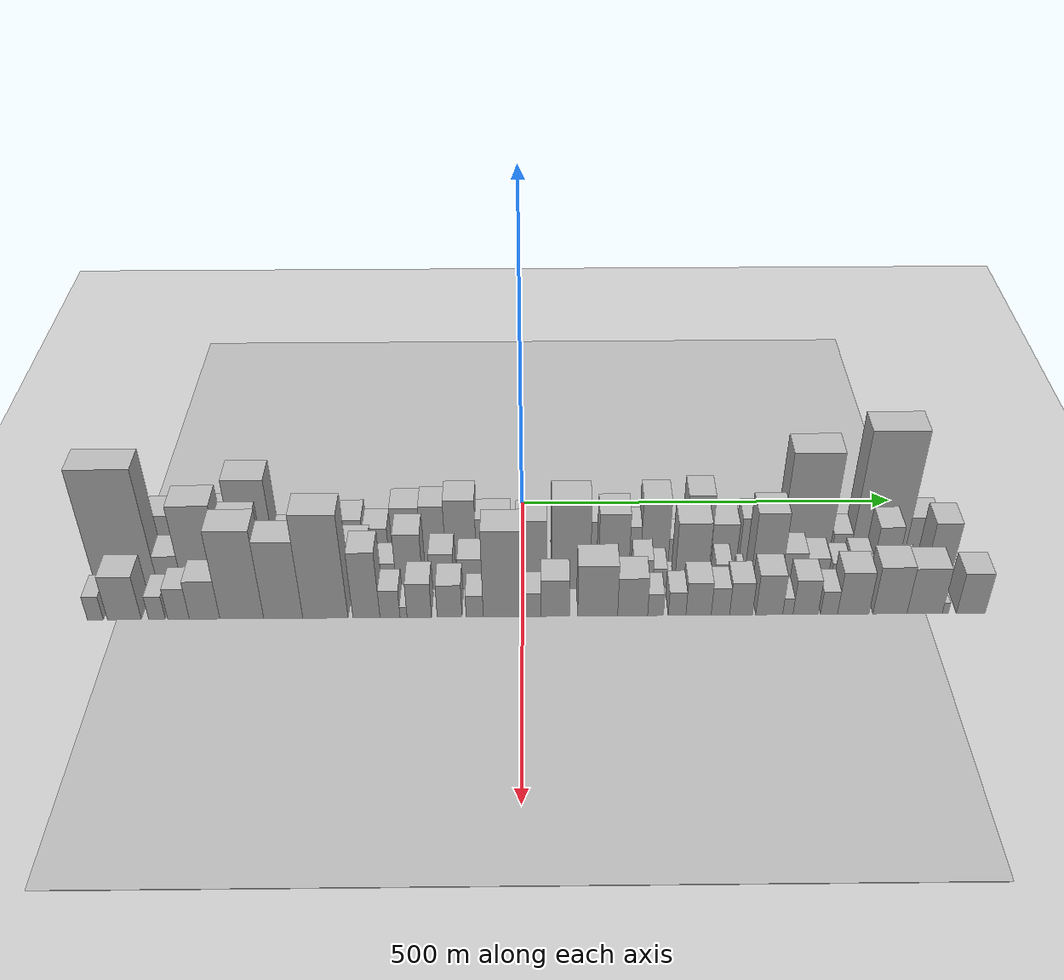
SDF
<?xml version="1.0" encoding="utf-8"?>

<sdf version="1.6">

   <world name="default">

      <gui fullscreen="0">

         <camera name="user_camera">

            <pose>-15 0 4.57585 0 0 0</pose>

            <view_controller>orbit</view_controller>

         </camera>

      </gui>

      <scene>

         <sky>

           <clouds>

             <speed>12</speed>

           </clouds>

         </sky>

         <ambient>0.4 0.4 0.4 1</ambient>

         <background>0.7 0.7 0.7 1</background>

         <shadows>1</shadows>

      </scene>

      <gravity>0 0 -9.8066</gravity>

      <magnetic_field>6e-06 2.3e-05 -4.2e-05</magnetic_field>

      <physics default="0" name="default_physics" type="ode">

         <ode>

            <solver>

               <type>quick</type>

               <iters>10</iters>

               <sor>1.0</sor>

               <use_dynamic_moi_rescaling>0</use_dynamic_moi_rescaling>

            </solver>

            <constraints>

               <cfm>0</cfm>

               <erp>0.2</erp>

               <contact_max_correcting_vel>100</contact_max_correcting_vel>

               <contact_surface_layer>0.001</contact_surface_layer>

            </constraints>

         </ode>

         <max_step_size>0.004</max_step_size>

         <real_time_factor>1</real_time_factor>

         <real_time_update_rate>250</real_time_update_rate>

      </physics>

      <light name="sun" type="directional">

         <cast_shadows>1</cast_shadows>

         <pose>0 0 10 0 0 0</pose>

         <diffuse>0.8 0.8 0.8 1</diffuse>

         <specular>0.2 0.2 0.2 1</specular>

         <attenuation>

            <range>1000</range>

            <constant>0.9</constant>

            <linear>0.01</linear>

            <quadratic>0.001</quadratic>

         </attenuation>

         <direction>-0.5 0.1 -0.9</direction>

      </light>

      <include>

         <name>ground_plane_1</name>

         <uri>model://HANNAS_ground_plane</uri>

         <pose>0 0 0  0 0 0</pose>

      </include>

      <include>

         <name>ground_plane_2</name>

         <uri>model://HANNAS_ground_plane</uri>

         <pose>100 0 0  0 0 0</pose>

      </include>

      <model name="building_1">

         <static>1</static>

         <pose frame="">100.0000 -519.6866 0 0.000000 0.000000 0.000000</pose>

         <link name="link">

            <pose frame="">0 0 13.50 0 0 0</pose>

            <collision name="collision">

               <geometry>

                  <box>

                     <size>40.0000 12.6267 27.0000</size>

                  </box>

               </geometry>

               <max_contacts>10</max_contacts>

               <surface>

                  <contact>

                     <ode/>

                  </contact>

                  <bounce/>

                  <friction>

                     <torsional>

                        <ode/>

                     </torsional>

                     <ode/>

                  </friction>

               </surface>

            </collision>

            <visual name="visual">

               <cast_shadows>0</cast_shadows>

               <geometry>

                  <box>

                     <size>40.0000 12.6267 27.0000</size>

                  </box>

               </geometry>

               <material>

                  <script>

                     <uri>model://HANNAS_wall/materials/scripts</uri>

                     <uri>model://HANNAS_wall/materials/textures</uri>

                     <name>vrc/HANNAS_wall</name>

                  </script>

               </material>

            </visual>

            <self_collide>0</self_collide>

            <enable_wind>0</enable_wind>

            <kinematic>0</kinematic>

         </link>

      </model>

      <model name="building_2">

         <static>1</static>

         <pose frame="">100.0000 -494.6154 0 0.000000 0.000000 0.000000</pose>

         <link name="link">

            <pose frame="">0 0 25.50 0 0 0</pose>

            <collision name="collision">

               <geometry>

                  <box>

                     <size>40.0000 25.5158 51.0000</size>

                  </box>

               </geometry>

               <max_contacts>10</max_contacts>

               <surface>

                  <contact>

                     <ode/>

                  </contact>

                  <bounce/>

                  <friction>

                     <torsional>

                        <ode/>

                     </torsional>

                     <ode/>

                  </friction>

               </surface>

            </collision>

            <visual name="visual">

               <cast_shadows>0</cast_shadows>

               <geometry>

                  <box>

                     <size>40.0000 25.5158 51.0000</size>

                  </box>

               </geometry>

               <material>

                  <script>

                     <uri>model://HANNAS_wall/materials/scripts</uri>

                     <uri>model://HANNAS_wall/materials/textures</uri>

                     <name>vrc/HANNAS_wall</name>

                  </script>

               </material>

            </visual>

            <self_collide>0</self_collide>

            <enable_wind>0</enable_wind>

            <kinematic>0</kinematic>

         </link>

      </model>

      <model name="building_3">

         <static>1</static>

         <pose frame="">100.0000 -450.8722 0 0.000000 0.000000 0.000000</pose>

         <link name="link">

            <pose frame="">0 0 42.00 0 0 0</pose>

            <collision name="collision">

               <geometry>

                  <box>

                     <size>40.0000 47.9705 84.0000</size>

                  </box>

               </geometry>

               <max_contacts>10</max_contacts>

               <surface>

                  <contact>

                     <ode/>

                  </contact>

                  <bounce/>

                  <friction>

                     <torsional>

                        <ode/>

                     </torsional>

                     <ode/>

                  </friction>

               </surface>

            </collision>

            <visual name="visual">

               <cast_shadows>0</cast_shadows>

               <geometry>

                  <box>

                     <size>40.0000 47.9705 84.0000</size>

                  </box>

               </geometry>

               <material>

                  <script>

                     <uri>model://HANNAS_wall/materials/scripts</uri>

                     <uri>model://HANNAS_wall/materials/textures</uri>

                     <name>vrc/HANNAS_wall</name>

                  </script>

               </material>

            </visual>

            <self_collide>0</self_collide>

            <enable_wind>0</enable_wind>

            <kinematic>0</kinematic>

         </link>

      </model>

      <model name="building_4">

         <static>1</static>

         <pose frame="">100.0000 -395.0757 0 0.000000 0.000000 0.000000</pose>

         <link name="link">

            <pose frame="">0 0 43.50 0 0 0</pose>

            <collision name="collision">

               <geometry>

                  <box>

                     <size>40.0000 49.6225 87.0000</size>

                  </box>

               </geometry>

               <max_contacts>10</max_contacts>

               <surface>

                  <contact>

                     <ode/>

                  </contact>

                  <bounce/>

                  <friction>

                     <torsional>

                        <ode/>

                     </torsional>

                     <ode/>

                  </friction>

               </surface>

            </collision>

            <visual name="visual">

               <cast_shadows>0</cast_shadows>

               <geometry>

                  <box>

                     <size>40.0000 49.6225 87.0000</size>

                  </box>

               </geometry>

               <material>

                  <script>

                     <uri>model://HANNAS_wall/materials/scripts</uri>

                     <uri>model://HANNAS_wall/materials/textures</uri>

                     <name>vrc/HANNAS_wall</name>

                  </script>

               </material>

            </visual>

            <self_collide>0</self_collide>

            <enable_wind>0</enable_wind>

            <kinematic>0</kinematic>

         </link>

      </model>

      <model name="building_5">

         <static>1</static>

         <pose frame="">100.0000 -343.9417 0 0.000000 0.000000 0.000000</pose>

         <link name="link">

            <pose frame="">0 0 70.50 0 0 0</pose>

            <collision name="collision">

               <geometry>

                  <box>

                     <size>40.0000 52.6456 141.0000</size>

                  </box>

               </geometry>

               <max_contacts>10</max_contacts>

               <surface>

                  <contact>

                     <ode/>

                  </contact>

                  <bounce/>

                  <friction>

                     <torsional>

                        <ode/>

                     </torsional>

                     <ode/>

                  </friction>

               </surface>

            </collision>

            <visual name="visual">

               <cast_shadows>0</cast_shadows>

               <geometry>

                  <box>

                     <size>40.0000 52.6456 141.0000</size>

                  </box>

               </geometry>

               <material>

                  <script>

                     <uri>model://HANNAS_wall/materials/scripts</uri>

                     <uri>model://HANNAS_wall/materials/textures</uri>

                     <name>vrc/HANNAS_wall</name>

                  </script>

               </material>

            </visual>

            <self_collide>0</self_collide>

            <enable_wind>0</enable_wind>

            <kinematic>0</kinematic>

         </link>

      </model>

      <model name="building_6">

         <static>1</static>

         <pose frame="">100.0000 -302.6311 0 0.000000 0.000000 0.000000</pose>

         <link name="link">

            <pose frame="">0 0 25.50 0 0 0</pose>

            <collision name="collision">

               <geometry>

                  <box>

                     <size>40.0000 29.9756 51.0000</size>

                  </box>

               </geometry>

               <max_contacts>10</max_contacts>

               <surface>

                  <contact>

                     <ode/>

                  </contact>

                  <bounce/>

                  <friction>

                     <torsional>

                        <ode/>

                     </torsional>

                     <ode/>

                  </friction>

               </surface>

            </collision>

            <visual name="visual">

               <cast_shadows>0</cast_shadows>

               <geometry>

                  <box>

                     <size>40.0000 29.9756 51.0000</size>

                  </box>

               </geometry>

               <material>

                  <script>

                     <uri>model://HANNAS_wall/materials/scripts</uri>

                     <uri>model://HANNAS_wall/materials/textures</uri>

                     <name>vrc/HANNAS_wall</name>

                  </script>

               </material>

            </visual>

            <self_collide>0</self_collide>

            <enable_wind>0</enable_wind>

            <kinematic>0</kinematic>

         </link>

      </model>

      <model name="building_7">

         <static>1</static>

         <pose frame="">100.0000 -263.2616 0 0.000000 0.000000 0.000000</pose>

         <link name="link">

            <pose frame="">0 0 36.00 0 0 0</pose>

            <collision name="collision">

               <geometry>

                  <box>

                     <size>40.0000 42.7635 72.0000</size>

                  </box>

               </geometry>

               <max_contacts>10</max_contacts>

               <surface>

                  <contact>

                     <ode/>

                  </contact>

                  <bounce/>

                  <friction>

                     <torsional>

                        <ode/>

                     </torsional>

                     <ode/>

                  </friction>

               </surface>

            </collision>

            <visual name="visual">

               <cast_shadows>0</cast_shadows>

               <geometry>

                  <box>

                     <size>40.0000 42.7635 72.0000</size>

                  </box>

               </geometry>

               <material>

                  <script>

                     <uri>model://HANNAS_wall/materials/scripts</uri>

                     <uri>model://HANNAS_wall/materials/textures</uri>

                     <name>vrc/HANNAS_wall</name>

                  </script>

               </material>

            </visual>

            <self_collide>0</self_collide>

            <enable_wind>0</enable_wind>

            <kinematic>0</kinematic>

         </link>

      </model>

      <model name="building_8">

         <static>1</static>

         <pose frame="">100.0000 -222.4727 0 0.000000 0.000000 0.000000</pose>

         <link name="link">

            <pose frame="">0 0 37.50 0 0 0</pose>

            <collision name="collision">

               <geometry>

                  <box>

                     <size>40.0000 38.8142 75.0000</size>

                  </box>

               </geometry>

               <max_contacts>10</max_contacts>

               <surface>

                  <contact>

                     <ode/>

                  </contact>

                  <bounce/>

                  <friction>

                     <torsional>

                        <ode/>

                     </torsional>

                     <ode/>

                  </friction>

               </surface>

            </collision>

            <visual name="visual">

               <cast_shadows>0</cast_shadows>

               <geometry>

                  <box>

                     <size>40.0000 38.8142 75.0000</size>

                  </box>

               </geometry>

               <material>

                  <script>

                     <uri>model://HANNAS_wall/materials/scripts</uri>

                     <uri>model://HANNAS_wall/materials/textures</uri>

                     <name>vrc/HANNAS_wall</name>

                  </script>

               </material>

            </visual>

            <self_collide>0</self_collide>

            <enable_wind>0</enable_wind>

            <kinematic>0</kinematic>

         </link>

      </model>

      <model name="building_9">

         <static>1</static>

         <pose frame="">100.0000 -187.4194 0 0.000000 0.000000 0.000000</pose>

         <link name="link">

            <pose frame="">0 0 30.00 0 0 0</pose>

            <collision name="collision">

               <geometry>

                  <box>

                     <size>40.0000 31.2924 60.0000</size>

                  </box>

               </geometry>

               <max_contacts>10</max_contacts>

               <surface>

                  <contact>

                     <ode/>

                  </contact>

                  <bounce/>

                  <friction>

                     <torsional>

                        <ode/>

                     </torsional>

                     <ode/>

                  </friction>

               </surface>

            </collision>

            <visual name="visual">

               <cast_shadows>0</cast_shadows>

               <geometry>

                  <box>

                     <size>40.0000 31.2924 60.0000</size>

                  </box>

               </geometry>

               <material>

                  <script>

                     <uri>model://HANNAS_wall/materials/scripts</uri>

                     <uri>model://HANNAS_wall/materials/textures</uri>

                     <name>vrc/HANNAS_wall</name>

                  </script>

               </material>

            </visual>

            <self_collide>0</self_collide>

            <enable_wind>0</enable_wind>

            <kinematic>0</kinematic>

         </link>

      </model>

      <model name="building_10">

         <static>1</static>

         <pose frame="">100.0000 -148.5886 0 0.000000 0.000000 0.000000</pose>

         <link name="link">

            <pose frame="">0 0 46.50 0 0 0</pose>

            <collision name="collision">

               <geometry>

                  <box>

                     <size>40.0000 36.3691 93.0000</size>

                  </box>

               </geometry>

               <max_contacts>10</max_contacts>

               <surface>

                  <contact>

                     <ode/>

                  </contact>

                  <bounce/>

                  <friction>

                     <torsional>

                        <ode/>

                     </torsional>

                     <ode/>

                  </friction>

               </surface>

            </collision>

            <visual name="visual">

               <cast_shadows>0</cast_shadows>

               <geometry>

                  <box>

                     <size>40.0000 36.3691 93.0000</size>

                  </box>

               </geometry>

               <material>

                  <script>

                     <uri>model://HANNAS_wall/materials/scripts</uri>

                     <uri>model://HANNAS_wall/materials/textures</uri>

                     <name>vrc/HANNAS_wall</name>

                  </script>

               </material>

            </visual>

            <self_collide>0</self_collide>

            <enable_wind>0</enable_wind>

            <kinematic>0</kinematic>

         </link>

      </model>

      <model name="building_11">

         <static>1</static>

         <pose frame="">100.0000 -114.7853 0 0.000000 0.000000 0.000000</pose>

         <link name="link">

            <pose frame="">0 0 48.00 0 0 0</pose>

            <collision name="collision">

               <geometry>

                  <box>

                     <size>40.0000 31.2376 96.0000</size>

                  </box>

               </geometry>

               <max_contacts>10</max_contacts>

               <surface>

                  <contact>

                     <ode/>

                  </contact>

                  <bounce/>

                  <friction>

                     <torsional>

                        <ode/>

                     </torsional>

                     <ode/>

                  </friction>

               </surface>

            </collision>

            <visual name="visual">

               <cast_shadows>0</cast_shadows>

               <geometry>

                  <box>

                     <size>40.0000 31.2376 96.0000</size>

                  </box>

               </geometry>

               <material>

                  <script>

                     <uri>model://HANNAS_wall/materials/scripts</uri>

                     <uri>model://HANNAS_wall/materials/textures</uri>

                     <name>vrc/HANNAS_wall</name>

                  </script>

               </material>

            </visual>

            <self_collide>0</self_collide>

            <enable_wind>0</enable_wind>

            <kinematic>0</kinematic>

         </link>

      </model>

      <model name="building_12">

         <static>1</static>

         <pose frame="">100.0000 -79.3528 0 0.000000 0.000000 0.000000</pose>

         <link name="link">

            <pose frame="">0 0 52.50 0 0 0</pose>

            <collision name="collision">

               <geometry>

                  <box>

                     <size>40.0000 39.6273 105.0000</size>

                  </box>

               </geometry>

               <max_contacts>10</max_contacts>

               <surface>

                  <contact>

                     <ode/>

                  </contact>

                  <bounce/>

                  <friction>

                     <torsional>

                        <ode/>

                     </torsional>

                     <ode/>

                  </friction>

               </surface>

            </collision>

            <visual name="visual">

               <cast_shadows>0</cast_shadows>

               <geometry>

                  <box>

                     <size>40.0000 39.6273 105.0000</size>

                  </box>

               </geometry>

               <material>

                  <script>

                     <uri>model://HANNAS_wall/materials/scripts</uri>

                     <uri>model://HANNAS_wall/materials/textures</uri>

                     <name>vrc/HANNAS_wall</name>

                  </script>

               </material>

            </visual>

            <self_collide>0</self_collide>

            <enable_wind>0</enable_wind>

            <kinematic>0</kinematic>

         </link>

      </model>

      <model name="building_13">

         <static>1</static>

         <pose frame="">100.0000 -37.3916 0 0.000000 0.000000 0.000000</pose>

         <link name="link">

            <pose frame="">0 0 37.50 0 0 0</pose>

            <collision name="collision">

               <geometry>

                  <box>

                     <size>40.0000 44.2951 75.0000</size>

                  </box>

               </geometry>

               <max_contacts>10</max_contacts>

               <surface>

                  <contact>

                     <ode/>

                  </contact>

                  <bounce/>

                  <friction>

                     <torsional>

                        <ode/>

                     </torsional>

                     <ode/>

                  </friction>

               </surface>

            </collision>

            <visual name="visual">

               <cast_shadows>0</cast_shadows>

               <geometry>

                  <box>

                     <size>40.0000 44.2951 75.0000</size>

                  </box>

               </geometry>

               <material>

                  <script>

                     <uri>model://HANNAS_wall/materials/scripts</uri>

                     <uri>model://HANNAS_wall/materials/textures</uri>

                     <name>vrc/HANNAS_wall</name>

                  </script>

               </material>

            </visual>

            <self_collide>0</self_collide>

            <enable_wind>0</enable_wind>

            <kinematic>0</kinematic>

         </link>

      </model>

      <model name="building_14">

         <static>1</static>

         <pose frame="">100.0000 5.1237 0 0.000000 0.000000 0.000000</pose>

         <link name="link">

            <pose frame="">0 0 21.00 0 0 0</pose>

            <collision name="collision">

               <geometry>

                  <box>

                     <size>40.0000 22.7354 42.0000</size>

                  </box>

               </geometry>

               <max_contacts>10</max_contacts>

               <surface>

                  <contact>

                     <ode/>

                  </contact>

                  <bounce/>

                  <friction>

                     <torsional>

                        <ode/>

                     </torsional>

                     <ode/>

                  </friction>

               </surface>

            </collision>

            <visual name="visual">

               <cast_shadows>0</cast_shadows>

               <geometry>

                  <box>

                     <size>40.0000 22.7354 42.0000</size>

                  </box>

               </geometry>

               <material>

                  <script>

                     <uri>model://HANNAS_wall/materials/scripts</uri>

                     <uri>model://HANNAS_wall/materials/textures</uri>

                     <name>vrc/HANNAS_wall</name>

                  </script>

               </material>

            </visual>

            <self_collide>0</self_collide>

            <enable_wind>0</enable_wind>

            <kinematic>0</kinematic>

         </link>

      </model>

      <model name="building_15">

         <static>1</static>

         <pose frame="">100.0000 23.2030 0 0.000000 0.000000 0.000000</pose>

         <link name="link">

            <pose frame="">0 0 13.50 0 0 0</pose>

            <collision name="collision">

               <geometry>

                  <box>

                     <size>40.0000 13.4233 27.0000</size>

                  </box>

               </geometry>

               <max_contacts>10</max_contacts>

               <surface>

                  <contact>

                     <ode/>

                  </contact>

                  <bounce/>

                  <friction>

                     <torsional>

                        <ode/>

                     </torsional>

                     <ode/>

                  </friction>

               </surface>

            </collision>

            <visual name="visual">

               <cast_shadows>0</cast_shadows>

               <geometry>

                  <box>

                     <size>40.0000 13.4233 27.0000</size>

                  </box>

               </geometry>

               <material>

                  <script>

                     <uri>model://HANNAS_wall/materials/scripts</uri>

                     <uri>model://HANNAS_wall/materials/textures</uri>

                     <name>vrc/HANNAS_wall</name>

                  </script>

               </material>

            </visual>

            <self_collide>0</self_collide>

            <enable_wind>0</enable_wind>

            <kinematic>0</kinematic>

         </link>

      </model>

      <model name="building_16">

         <static>1</static>

         <pose frame="">100.0000 47.8059 0 0.000000 0.000000 0.000000</pose>

         <link name="link">

            <pose frame="">0 0 19.50 0 0 0</pose>

            <collision name="collision">

               <geometry>

                  <box>

                     <size>40.0000 21.7824 39.0000</size>

                  </box>

               </geometry>

               <max_contacts>10</max_contacts>

               <surface>

                  <contact>

                     <ode/>

                  </contact>

                  <bounce/>

                  <friction>

                     <torsional>

                        <ode/>

                     </torsional>

                     <ode/>

                  </friction>

               </surface>

            </collision>

            <visual name="visual">

               <cast_shadows>0</cast_shadows>

               <geometry>

                  <box>

                     <size>40.0000 21.7824 39.0000</size>

                  </box>

               </geometry>

               <material>

                  <script>

                     <uri>model://HANNAS_wall/materials/scripts</uri>

                     <uri>model://HANNAS_wall/materials/textures</uri>

                     <name>vrc/HANNAS_wall</name>

                  </script>

               </material>

            </visual>

            <self_collide>0</self_collide>

            <enable_wind>0</enable_wind>

            <kinematic>0</kinematic>

         </link>

      </model>

      <model name="building_17">

         <static>1</static>

         <pose frame="">100.0000 81.5890 0 0.000000 0.000000 0.000000</pose>

         <link name="link">

            <pose frame="">0 0 34.50 0 0 0</pose>

            <collision name="collision">

               <geometry>

                  <box>

                     <size>40.0000 37.7838 69.0000</size>

                  </box>

               </geometry>

               <max_contacts>10</max_contacts>

               <surface>

                  <contact>

                     <ode/>

                  </contact>

                  <bounce/>

                  <friction>

                     <torsional>

                        <ode/>

                     </torsional>

                     <ode/>

                  </friction>

               </surface>

            </collision>

            <visual name="visual">

               <cast_shadows>0</cast_shadows>

               <geometry>

                  <box>

                     <size>40.0000 37.7838 69.0000</size>

                  </box>

               </geometry>

               <material>

                  <script>

                     <uri>model://HANNAS_wall/materials/scripts</uri>

                     <uri>model://HANNAS_wall/materials/textures</uri>

                     <name>vrc/HANNAS_wall</name>

                  </script>

               </material>

            </visual>

            <self_collide>0</self_collide>

            <enable_wind>0</enable_wind>

            <kinematic>0</kinematic>

         </link>

      </model>

      <model name="building_18">

         <static>1</static>

         <pose frame="">100.0000 110.0297 0 0.000000 0.000000 0.000000</pose>

         <link name="link">

            <pose frame="">0 0 18.00 0 0 0</pose>

            <collision name="collision">

               <geometry>

                  <box>

                     <size>40.0000 19.0977 36.0000</size>

                  </box>

               </geometry>

               <max_contacts>10</max_contacts>

               <surface>

                  <contact>

                     <ode/>

                  </contact>

                  <bounce/>

                  <friction>

                     <torsional>

                        <ode/>

                     </torsional>

                     <ode/>

                  </friction>

               </surface>

            </collision>

            <visual name="visual">

               <cast_shadows>0</cast_shadows>

               <geometry>

                  <box>

                     <size>40.0000 19.0977 36.0000</size>

                  </box>

               </geometry>

               <material>

                  <script>

                     <uri>model://HANNAS_wall/materials/scripts</uri>

                     <uri>model://HANNAS_wall/materials/textures</uri>

                     <name>vrc/HANNAS_wall</name>

                  </script>

               </material>

            </visual>

            <self_collide>0</self_collide>

            <enable_wind>0</enable_wind>

            <kinematic>0</kinematic>

         </link>

      </model>

      <model name="building_19">

         <static>1</static>

         <pose frame="">100.0000 137.6985 0 0.000000 0.000000 0.000000</pose>

         <link name="link">

            <pose frame="">0 0 30.00 0 0 0</pose>

            <collision name="collision">

               <geometry>

                  <box>

                     <size>40.0000 30.2399 60.0000</size>

                  </box>

               </geometry>

               <max_contacts>10</max_contacts>

               <surface>

                  <contact>

                     <ode/>

                  </contact>

                  <bounce/>

                  <friction>

                     <torsional>

                        <ode/>

                     </torsional>

                     <ode/>

                  </friction>

               </surface>

            </collision>

            <visual name="visual">

               <cast_shadows>0</cast_shadows>

               <geometry>

                  <box>

                     <size>40.0000 30.2399 60.0000</size>

                  </box>

               </geometry>

               <material>

                  <script>

                     <uri>model://HANNAS_wall/materials/scripts</uri>

                     <uri>model://HANNAS_wall/materials/textures</uri>

                     <name>vrc/HANNAS_wall</name>

                  </script>

               </material>

            </visual>

            <self_collide>0</self_collide>

            <enable_wind>0</enable_wind>

            <kinematic>0</kinematic>

         </link>

      </model>

      <model name="building_20">

         <static>1</static>

         <pose frame="">100.0000 170.7116 0 0.000000 0.000000 0.000000</pose>

         <link name="link">

            <pose frame="">0 0 52.50 0 0 0</pose>

            <collision name="collision">

               <geometry>

                  <box>

                     <size>40.0000 35.7862 105.0000</size>

                  </box>

               </geometry>

               <max_contacts>10</max_contacts>

               <surface>

                  <contact>

                     <ode/>

                  </contact>

                  <bounce/>

                  <friction>

                     <torsional>

                        <ode/>

                     </torsional>

                     <ode/>

                  </friction>

               </surface>

            </collision>

            <visual name="visual">

               <cast_shadows>0</cast_shadows>

               <geometry>

                  <box>

                     <size>40.0000 35.7862 105.0000</size>

                  </box>

               </geometry>

               <material>

                  <script>

                     <uri>model://HANNAS_wall/materials/scripts</uri>

                     <uri>model://HANNAS_wall/materials/textures</uri>

                     <name>vrc/HANNAS_wall</name>

                  </script>

               </material>

            </visual>

            <self_collide>0</self_collide>

            <enable_wind>0</enable_wind>

            <kinematic>0</kinematic>

         </link>

      </model>

      <model name="building_21">

         <static>1</static>

         <pose frame="">100.0000 198.8116 0 0.000000 0.000000 0.000000</pose>

         <link name="link">

            <pose frame="">0 0 19.50 0 0 0</pose>

            <collision name="collision">

               <geometry>

                  <box>

                     <size>40.0000 20.4138 39.0000</size>

                  </box>

               </geometry>

               <max_contacts>10</max_contacts>

               <surface>

                  <contact>

                     <ode/>

                  </contact>

                  <bounce/>

                  <friction>

                     <torsional>

                        <ode/>

                     </torsional>

                     <ode/>

                  </friction>

               </surface>

            </collision>

            <visual name="visual">

               <cast_shadows>0</cast_shadows>

               <geometry>

                  <box>

                     <size>40.0000 20.4138 39.0000</size>

                  </box>

               </geometry>

               <material>

                  <script>

                     <uri>model://HANNAS_wall/materials/scripts</uri>

                     <uri>model://HANNAS_wall/materials/textures</uri>

                     <name>vrc/HANNAS_wall</name>

                  </script>

               </material>

            </visual>

            <self_collide>0</self_collide>

            <enable_wind>0</enable_wind>

            <kinematic>0</kinematic>

         </link>

      </model>

      <model name="building_22">

         <static>1</static>

         <pose frame="">100.0000 226.1060 0 0.000000 0.000000 0.000000</pose>

         <link name="link">

            <pose frame="">0 0 55.50 0 0 0</pose>

            <collision name="collision">

               <geometry>

                  <box>

                     <size>40.0000 34.1748 111.0000</size>

                  </box>

               </geometry>

               <max_contacts>10</max_contacts>

               <surface>

                  <contact>

                     <ode/>

                  </contact>

                  <bounce/>

                  <friction>

                     <torsional>

                        <ode/>

                     </torsional>

                     <ode/>

                  </friction>

               </surface>

            </collision>

            <visual name="visual">

               <cast_shadows>0</cast_shadows>

               <geometry>

                  <box>

                     <size>40.0000 34.1748 111.0000</size>

                  </box>

               </geometry>

               <material>

                  <script>

                     <uri>model://HANNAS_wall/materials/scripts</uri>

                     <uri>model://HANNAS_wall/materials/textures</uri>

                     <name>vrc/HANNAS_wall</name>

                  </script>

               </material>

            </visual>

            <self_collide>0</self_collide>

            <enable_wind>0</enable_wind>

            <kinematic>0</kinematic>

         </link>

      </model>

      <model name="building_23">

         <static>1</static>

         <pose frame="">100.0000 260.1984 0 0.000000 0.000000 0.000000</pose>

         <link name="link">

            <pose frame="">0 0 31.50 0 0 0</pose>

            <collision name="collision">

               <geometry>

                  <box>

                     <size>40.0000 34.0099 63.0000</size>

                  </box>

               </geometry>

               <max_contacts>10</max_contacts>

               <surface>

                  <contact>

                     <ode/>

                  </contact>

                  <bounce/>

                  <friction>

                     <torsional>

                        <ode/>

                     </torsional>

                     <ode/>

                  </friction>

               </surface>

            </collision>

            <visual name="visual">

               <cast_shadows>0</cast_shadows>

               <geometry>

                  <box>

                     <size>40.0000 34.0099 63.0000</size>

                  </box>

               </geometry>

               <material>

                  <script>

                     <uri>model://HANNAS_wall/materials/scripts</uri>

                     <uri>model://HANNAS_wall/materials/textures</uri>

                     <name>vrc/HANNAS_wall</name>

                  </script>

               </material>

            </visual>

            <self_collide>0</self_collide>

            <enable_wind>0</enable_wind>

            <kinematic>0</kinematic>

         </link>

      </model>

      <model name="building_24">

         <static>1</static>

         <pose frame="">100.0000 300.5038 0 0.000000 0.000000 0.000000</pose>

         <link name="link">

            <pose frame="">0 0 36.00 0 0 0</pose>

            <collision name="collision">

               <geometry>

                  <box>

                     <size>40.0000 40.6009 72.0000</size>

                  </box>

               </geometry>

               <max_contacts>10</max_contacts>

               <surface>

                  <contact>

                     <ode/>

                  </contact>

                  <bounce/>

                  <friction>

                     <torsional>

                        <ode/>

                     </torsional>

                     <ode/>

                  </friction>

               </surface>

            </collision>

            <visual name="visual">

               <cast_shadows>0</cast_shadows>

               <geometry>

                  <box>

                     <size>40.0000 40.6009 72.0000</size>

                  </box>

               </geometry>

               <material>

                  <script>

                     <uri>model://HANNAS_wall/materials/scripts</uri>

                     <uri>model://HANNAS_wall/materials/textures</uri>

                     <name>vrc/HANNAS_wall</name>

                  </script>

               </material>

            </visual>

            <self_collide>0</self_collide>

            <enable_wind>0</enable_wind>

            <kinematic>0</kinematic>

         </link>

      </model>

      <model name="building_25">

         <static>1</static>

         <pose frame="">100.0000 329.2157 0 0.000000 0.000000 0.000000</pose>

         <link name="link">

            <pose frame="">0 0 7.50 0 0 0</pose>

            <collision name="collision">

               <geometry>

                  <box>

                     <size>40.0000 6.8229 15.0000</size>

                  </box>

               </geometry>

               <max_contacts>10</max_contacts>

               <surface>

                  <contact>

                     <ode/>

                  </contact>

                  <bounce/>

                  <friction>

                     <torsional>

                        <ode/>

                     </torsional>

                     <ode/>

                  </friction>

               </surface>

            </collision>

            <visual name="visual">

               <cast_shadows>0</cast_shadows>

               <geometry>

                  <box>

                     <size>40.0000 6.8229 15.0000</size>

                  </box>

               </geometry>

               <material>

                  <script>

                     <uri>model://HANNAS_wall/materials/scripts</uri>

                     <uri>model://HANNAS_wall/materials/textures</uri>

                     <name>vrc/HANNAS_wall</name>

                  </script>

               </material>

            </visual>

            <self_collide>0</self_collide>

            <enable_wind>0</enable_wind>

            <kinematic>0</kinematic>

         </link>

      </model>

      <model name="building_26">

         <static>1</static>

         <pose frame="">100.0000 364.3298 0 0.000000 0.000000 0.000000</pose>

         <link name="link">

            <pose frame="">0 0 88.50 0 0 0</pose>

            <collision name="collision">

               <geometry>

                  <box>

                     <size>40.0000 63.4053 177.0000</size>

                  </box>

               </geometry>

               <max_contacts>10</max_contacts>

               <surface>

                  <contact>

                     <ode/>

                  </contact>

                  <bounce/>

                  <friction>

                     <torsional>

                        <ode/>

                     </torsional>

                     <ode/>

                  </friction>

               </surface>

            </collision>

            <visual name="visual">

               <cast_shadows>0</cast_shadows>

               <geometry>

                  <box>

                     <size>40.0000 63.4053 177.0000</size>

                  </box>

               </geometry>

               <material>

                  <script>

                     <uri>model://HANNAS_wall/materials/scripts</uri>

                     <uri>model://HANNAS_wall/materials/textures</uri>

                     <name>vrc/HANNAS_wall</name>

                  </script>

               </material>

            </visual>

            <self_collide>0</self_collide>

            <enable_wind>0</enable_wind>

            <kinematic>0</kinematic>

         </link>

      </model>

      <model name="building_27">

         <static>1</static>

         <pose frame="">100.0000 411.1410 0 0.000000 0.000000 0.000000</pose>

         <link name="link">

            <pose frame="">0 0 22.50 0 0 0</pose>

            <collision name="collision">

               <geometry>

                  <box>

                     <size>40.0000 24.2172 45.0000</size>

                  </box>

               </geometry>

               <max_contacts>10</max_contacts>

               <surface>

                  <contact>

                     <ode/>

                  </contact>

                  <bounce/>

                  <friction>

                     <torsional>

                        <ode/>

                     </torsional>

                     <ode/>

                  </friction>

               </surface>

            </collision>

            <visual name="visual">

               <cast_shadows>0</cast_shadows>

               <geometry>

                  <box>

                     <size>40.0000 24.2172 45.0000</size>

                  </box>

               </geometry>

               <material>

                  <script>

                     <uri>model://HANNAS_wall/materials/scripts</uri>

                     <uri>model://HANNAS_wall/materials/textures</uri>

                     <name>vrc/HANNAS_wall</name>

                  </script>

               </material>

            </visual>

            <self_collide>0</self_collide>

            <enable_wind>0</enable_wind>

            <kinematic>0</kinematic>

         </link>

      </model>

      <model name="building_28">

         <static>1</static>

         <pose frame="">100.0000 458.4552 0 0.000000 0.000000 0.000000</pose>

         <link name="link">

            <pose frame="">0 0 105.00 0 0 0</pose>

            <collision name="collision">

               <geometry>

                  <box>

                     <size>40.0000 70.4112 210.0000</size>

                  </box>

               </geometry>

               <max_contacts>10</max_contacts>

               <surface>

                  <contact>

                     <ode/>

                  </contact>

                  <bounce/>

                  <friction>

                     <torsional>

                        <ode/>

                     </torsional>

                     <ode/>

                  </friction>

               </surface>

            </collision>

            <visual name="visual">

               <cast_shadows>0</cast_shadows>

               <geometry>

                  <box>

                     <size>40.0000 70.4112 210.0000</size>

                  </box>

               </geometry>

               <material>

                  <script>

                     <uri>model://HANNAS_wall/materials/scripts</uri>

                     <uri>model://HANNAS_wall/materials/textures</uri>

                     <name>vrc/HANNAS_wall</name>

                  </script>

               </material>

            </visual>

            <self_collide>0</self_collide>

            <enable_wind>0</enable_wind>

            <kinematic>0</kinematic>

         </link>

      </model>

      <model name="building_29">

         <static>1</static>

         <pose frame="">100.0000 511.9510 0 0.000000 0.000000 0.000000</pose>

         <link name="link">

            <pose frame="">0 0 36.00 0 0 0</pose>

            <collision name="collision">

               <geometry>

                  <box>

                     <size>40.0000 36.5804 72.0000</size>

                  </box>

               </geometry>

               <max_contacts>10</max_contacts>

               <surface>

                  <contact>

                     <ode/>

                  </contact>

                  <bounce/>

                  <friction>

                     <torsional>

                        <ode/>

                     </torsional>

                     <ode/>

                  </friction>

               </surface>

            </collision>

            <visual name="visual">

               <cast_shadows>0</cast_shadows>

               <geometry>

                  <box>

                     <size>40.0000 36.5804 72.0000</size>

                  </box>

               </geometry>

               <material>

                  <script>

                     <uri>model://HANNAS_wall/materials/scripts</uri>

                     <uri>model://HANNAS_wall/materials/textures</uri>

                     <name>vrc/HANNAS_wall</name>

                  </script>

               </material>

            </visual>

            <self_collide>0</self_collide>

            <enable_wind>0</enable_wind>

            <kinematic>0</kinematic>

         </link>

      </model>

      <model name="building_30">

         <static>1</static>

         <pose frame="">100.0000 539.8981 0 0.000000 0.000000 0.000000</pose>

         <link name="link">

            <pose frame="">0 0 16.50 0 0 0</pose>

            <collision name="collision">

               <geometry>

                  <box>

                     <size>40.0000 19.3137 33.0000</size>

                  </box>

               </geometry>

               <max_contacts>10</max_contacts>

               <surface>

                  <contact>

                     <ode/>

                  </contact>

                  <bounce/>

                  <friction>

                     <torsional>

                        <ode/>

                     </torsional>

                     <ode/>

                  </friction>

               </surface>

            </collision>

            <visual name="visual">

               <cast_shadows>0</cast_shadows>

               <geometry>

                  <box>

                     <size>40.0000 19.3137 33.0000</size>

                  </box>

               </geometry>

               <material>

                  <script>

                     <uri>model://HANNAS_wall/materials/scripts</uri>

                     <uri>model://HANNAS_wall/materials/textures</uri>

                     <name>vrc/HANNAS_wall</name>

                  </script>

               </material>

            </visual>

            <self_collide>0</self_collide>

            <enable_wind>0</enable_wind>

            <kinematic>0</kinematic>

         </link>

      </model>

      <model name="building_31">

         <static>1</static>

         <pose frame="">149.0000 -497.0887 0 0.000000 0.000000 0.000000</pose>

         <link name="link">

            <pose frame="">0 0 99.00 0 0 0</pose>

            <collision name="collision">

               <geometry>

                  <box>

                     <size>40.0000 77.8226 198.0000</size>

                  </box>

               </geometry>

               <max_contacts>10</max_contacts>

               <surface>

                  <contact>

                     <ode/>

                  </contact>

                  <bounce/>

                  <friction>

                     <torsional>

                        <ode/>

                     </torsional>

                     <ode/>

                  </friction>

               </surface>

            </collision>

            <visual name="visual">

               <cast_shadows>0</cast_shadows>

               <geometry>

                  <box>

                     <size>40.0000 77.8226 198.0000</size>

                  </box>

               </geometry>

               <material>

                  <script>

                     <uri>model://HANNAS_wall/materials/scripts</uri>

                     <uri>model://HANNAS_wall/materials/textures</uri>

                     <name>vrc/HANNAS_wall</name>

                  </script>

               </material>

            </visual>

            <self_collide>0</self_collide>

            <enable_wind>0</enable_wind>

            <kinematic>0</kinematic>

         </link>

      </model>

      <model name="building_32">

         <static>1</static>

         <pose frame="">149.0000 -442.9070 0 0.000000 0.000000 0.000000</pose>

         <link name="link">

            <pose frame="">0 0 30.00 0 0 0</pose>

            <collision name="collision">

               <geometry>

                  <box>

                     <size>40.0000 30.5407 60.0000</size>

                  </box>

               </geometry>

               <max_contacts>10</max_contacts>

               <surface>

                  <contact>

                     <ode/>

                  </contact>

                  <bounce/>

                  <friction>

                     <torsional>

                        <ode/>

                     </torsional>

                     <ode/>

                  </friction>

               </surface>

            </collision>

            <visual name="visual">

               <cast_shadows>0</cast_shadows>

               <geometry>

                  <box>

                     <size>40.0000 30.5407 60.0000</size>

                  </box>

               </geometry>

               <material>

                  <script>

                     <uri>model://HANNAS_wall/materials/scripts</uri>

                     <uri>model://HANNAS_wall/materials/textures</uri>

                     <name>vrc/HANNAS_wall</name>

                  </script>

               </material>

            </visual>

            <self_collide>0</self_collide>

            <enable_wind>0</enable_wind>

            <kinematic>0</kinematic>

         </link>

      </model>

      <model name="building_33">

         <static>1</static>

         <pose frame="">149.0000 -401.4704 0 0.000000 0.000000 0.000000</pose>

         <link name="link">

            <pose frame="">0 0 70.50 0 0 0</pose>

            <collision name="collision">

               <geometry>

                  <box>

                     <size>40.0000 52.3324 141.0000</size>

                  </box>

               </geometry>

               <max_contacts>10</max_contacts>

               <surface>

                  <contact>

                     <ode/>

                  </contact>

                  <bounce/>

                  <friction>

                     <torsional>

                        <ode/>

                     </torsional>

                     <ode/>

                  </friction>

               </surface>

            </collision>

            <visual name="visual">

               <cast_shadows>0</cast_shadows>

               <geometry>

                  <box>

                     <size>40.0000 52.3324 141.0000</size>

                  </box>

               </geometry>

               <material>

                  <script>

                     <uri>model://HANNAS_wall/materials/scripts</uri>

                     <uri>model://HANNAS_wall/materials/textures</uri>

                     <name>vrc/HANNAS_wall</name>

                  </script>

               </material>

            </visual>

            <self_collide>0</self_collide>

            <enable_wind>0</enable_wind>

            <kinematic>0</kinematic>

         </link>

      </model>

      <model name="building_34">

         <static>1</static>

         <pose frame="">149.0000 -352.8237 0 0.000000 0.000000 0.000000</pose>

         <link name="link">

            <pose frame="">0 0 57.00 0 0 0</pose>

            <collision name="collision">

               <geometry>

                  <box>

                     <size>40.0000 44.9612 114.0000</size>

                  </box>

               </geometry>

               <max_contacts>10</max_contacts>

               <surface>

                  <contact>

                     <ode/>

                  </contact>

                  <bounce/>

                  <friction>

                     <torsional>

                        <ode/>

                     </torsional>

                     <ode/>

                  </friction>

               </surface>

            </collision>

            <visual name="visual">

               <cast_shadows>0</cast_shadows>

               <geometry>

                  <box>

                     <size>40.0000 44.9612 114.0000</size>

                  </box>

               </geometry>

               <material>

                  <script>

                     <uri>model://HANNAS_wall/materials/scripts</uri>

                     <uri>model://HANNAS_wall/materials/textures</uri>

                     <name>vrc/HANNAS_wall</name>

                  </script>

               </material>

            </visual>

            <self_collide>0</self_collide>

            <enable_wind>0</enable_wind>

            <kinematic>0</kinematic>

         </link>

      </model>

      <model name="building_35">

         <static>1</static>

         <pose frame="">149.0000 -317.1891 0 0.000000 0.000000 0.000000</pose>

         <link name="link">

            <pose frame="">0 0 25.50 0 0 0</pose>

            <collision name="collision">

               <geometry>

                  <box>

                     <size>40.0000 26.3079 51.0000</size>

                  </box>

               </geometry>

               <max_contacts>10</max_contacts>

               <surface>

                  <contact>

                     <ode/>

                  </contact>

                  <bounce/>

                  <friction>

                     <torsional>

                        <ode/>

                     </torsional>

                     <ode/>

                  </friction>

               </surface>

            </collision>

            <visual name="visual">

               <cast_shadows>0</cast_shadows>

               <geometry>

                  <box>

                     <size>40.0000 26.3079 51.0000</size>

                  </box>

               </geometry>

               <material>

                  <script>

                     <uri>model://HANNAS_wall/materials/scripts</uri>

                     <uri>model://HANNAS_wall/materials/textures</uri>

                     <name>vrc/HANNAS_wall</name>

                  </script>

               </material>

            </visual>

            <self_collide>0</self_collide>

            <enable_wind>0</enable_wind>

            <kinematic>0</kinematic>

         </link>

      </model>

      <model name="building_36">

         <static>1</static>

         <pose frame="">149.0000 -282.0252 0 0.000000 0.000000 0.000000</pose>

         <link name="link">

            <pose frame="">0 0 37.50 0 0 0</pose>

            <collision name="collision">

               <geometry>

                  <box>

                     <size>40.0000 44.0200 75.0000</size>

                  </box>

               </geometry>

               <max_contacts>10</max_contacts>

               <surface>

                  <contact>

                     <ode/>

                  </contact>

                  <bounce/>

                  <friction>

                     <torsional>

                        <ode/>

                     </torsional>

                     <ode/>

                  </friction>

               </surface>

            </collision>

            <visual name="visual">

               <cast_shadows>0</cast_shadows>

               <geometry>

                  <box>

                     <size>40.0000 44.0200 75.0000</size>

                  </box>

               </geometry>

               <material>

                  <script>

                     <uri>model://HANNAS_wall/materials/scripts</uri>

                     <uri>model://HANNAS_wall/materials/textures</uri>

                     <name>vrc/HANNAS_wall</name>

                  </script>

               </material>

            </visual>

            <self_collide>0</self_collide>

            <enable_wind>0</enable_wind>

            <kinematic>0</kinematic>

         </link>

      </model>

      <model name="building_37">

         <static>1</static>

         <pose frame="">149.0000 -246.9999 0 0.000000 0.000000 0.000000</pose>

         <link name="link">

            <pose frame="">0 0 22.50 0 0 0</pose>

            <collision name="collision">

               <geometry>

                  <box>

                     <size>40.0000 26.0306 45.0000</size>

                  </box>

               </geometry>

               <max_contacts>10</max_contacts>

               <surface>

                  <contact>

                     <ode/>

                  </contact>

                  <bounce/>

                  <friction>

                     <torsional>

                        <ode/>

                     </torsional>

                     <ode/>

                  </friction>

               </surface>

            </collision>

            <visual name="visual">

               <cast_shadows>0</cast_shadows>

               <geometry>

                  <box>

                     <size>40.0000 26.0306 45.0000</size>

                  </box>

               </geometry>

               <material>

                  <script>

                     <uri>model://HANNAS_wall/materials/scripts</uri>

                     <uri>model://HANNAS_wall/materials/textures</uri>

                     <name>vrc/HANNAS_wall</name>

                  </script>

               </material>

            </visual>

            <self_collide>0</self_collide>

            <enable_wind>0</enable_wind>

            <kinematic>0</kinematic>

         </link>

      </model>

      <model name="building_38">

         <static>1</static>

         <pose frame="">149.0000 -212.6889 0 0.000000 0.000000 0.000000</pose>

         <link name="link">

            <pose frame="">0 0 37.50 0 0 0</pose>

            <collision name="collision">

               <geometry>

                  <box>

                     <size>40.0000 42.5914 75.0000</size>

                  </box>

               </geometry>

               <max_contacts>10</max_contacts>

               <surface>

                  <contact>

                     <ode/>

                  </contact>

                  <bounce/>

                  <friction>

                     <torsional>

                        <ode/>

                     </torsional>

                     <ode/>

                  </friction>

               </surface>

            </collision>

            <visual name="visual">

               <cast_shadows>0</cast_shadows>

               <geometry>

                  <box>

                     <size>40.0000 42.5914 75.0000</size>

                  </box>

               </geometry>

               <material>

                  <script>

                     <uri>model://HANNAS_wall/materials/scripts</uri>

                     <uri>model://HANNAS_wall/materials/textures</uri>

                     <name>vrc/HANNAS_wall</name>

                  </script>

               </material>

            </visual>

            <self_collide>0</self_collide>

            <enable_wind>0</enable_wind>

            <kinematic>0</kinematic>

         </link>

      </model>

      <model name="building_39">

         <static>1</static>

         <pose frame="">149.0000 -170.6452 0 0.000000 0.000000 0.000000</pose>

         <link name="link">

            <pose frame="">0 0 22.50 0 0 0</pose>

            <collision name="collision">

               <geometry>

                  <box>

                     <size>40.0000 23.4961 45.0000</size>

                  </box>

               </geometry>

               <max_contacts>10</max_contacts>

               <surface>

                  <contact>

                     <ode/>

                  </contact>

                  <bounce/>

                  <friction>

                     <torsional>

                        <ode/>

                     </torsional>

                     <ode/>

                  </friction>

               </surface>

            </collision>

            <visual name="visual">

               <cast_shadows>0</cast_shadows>

               <geometry>

                  <box>

                     <size>40.0000 23.4961 45.0000</size>

                  </box>

               </geometry>

               <material>

                  <script>

                     <uri>model://HANNAS_wall/materials/scripts</uri>

                     <uri>model://HANNAS_wall/materials/textures</uri>

                     <name>vrc/HANNAS_wall</name>

                  </script>

               </material>

            </visual>

            <self_collide>0</self_collide>

            <enable_wind>0</enable_wind>

            <kinematic>0</kinematic>

         </link>

      </model>

      <model name="building_40">

         <static>1</static>

         <pose frame="">149.0000 -142.1918 0 0.000000 0.000000 0.000000</pose>

         <link name="link">

            <pose frame="">0 0 46.50 0 0 0</pose>

            <collision name="collision">

               <geometry>

                  <box>

                     <size>40.0000 33.4107 93.0000</size>

                  </box>

               </geometry>

               <max_contacts>10</max_contacts>

               <surface>

                  <contact>

                     <ode/>

                  </contact>

                  <bounce/>

                  <friction>

                     <torsional>

                        <ode/>

                     </torsional>

                     <ode/>

                  </friction>

               </surface>

            </collision>

            <visual name="visual">

               <cast_shadows>0</cast_shadows>

               <geometry>

                  <box>

                     <size>40.0000 33.4107 93.0000</size>

                  </box>

               </geometry>

               <material>

                  <script>

                     <uri>model://HANNAS_wall/materials/scripts</uri>

                     <uri>model://HANNAS_wall/materials/textures</uri>

                     <name>vrc/HANNAS_wall</name>

                  </script>

               </material>

            </visual>

            <self_collide>0</self_collide>

            <enable_wind>0</enable_wind>

            <kinematic>0</kinematic>

         </link>

      </model>

      <model name="building_41">

         <static>1</static>

         <pose frame="">149.0000 -101.2283 0 0.000000 0.000000 0.000000</pose>

         <link name="link">

            <pose frame="">0 0 30.00 0 0 0</pose>

            <collision name="collision">

               <geometry>

                  <box>

                     <size>40.0000 30.5162 60.0000</size>

                  </box>

               </geometry>

               <max_contacts>10</max_contacts>

               <surface>

                  <contact>

                     <ode/>

                  </contact>

                  <bounce/>

                  <friction>

                     <torsional>

                        <ode/>

                     </torsional>

                     <ode/>

                  </friction>

               </surface>

            </collision>

            <visual name="visual">

               <cast_shadows>0</cast_shadows>

               <geometry>

                  <box>

                     <size>40.0000 30.5162 60.0000</size>

                  </box>

               </geometry>

               <material>

                  <script>

                     <uri>model://HANNAS_wall/materials/scripts</uri>

                     <uri>model://HANNAS_wall/materials/textures</uri>

                     <name>vrc/HANNAS_wall</name>

                  </script>

               </material>

            </visual>

            <self_collide>0</self_collide>

            <enable_wind>0</enable_wind>

            <kinematic>0</kinematic>

         </link>

      </model>

      <model name="building_42">

         <static>1</static>

         <pose frame="">149.0000 -65.9850 0 0.000000 0.000000 0.000000</pose>

         <link name="link">

            <pose frame="">0 0 25.50 0 0 0</pose>

            <collision name="collision">

               <geometry>

                  <box>

                     <size>40.0000 29.9704 51.0000</size>

                  </box>

               </geometry>

               <max_contacts>10</max_contacts>

               <surface>

                  <contact>

                     <ode/>

                  </contact>

                  <bounce/>

                  <friction>

                     <torsional>

                        <ode/>

                     </torsional>

                     <ode/>

                  </friction>

               </surface>

            </collision>

            <visual name="visual">

               <cast_shadows>0</cast_shadows>

               <geometry>

                  <box>

                     <size>40.0000 29.9704 51.0000</size>

                  </box>

               </geometry>

               <material>

                  <script>

                     <uri>model://HANNAS_wall/materials/scripts</uri>

                     <uri>model://HANNAS_wall/materials/textures</uri>

                     <name>vrc/HANNAS_wall</name>

                  </script>

               </material>

            </visual>

            <self_collide>0</self_collide>

            <enable_wind>0</enable_wind>

            <kinematic>0</kinematic>

         </link>

      </model>

      <model name="building_43">

         <static>1</static>

         <pose frame="">149.0000 -36.1388 0 0.000000 0.000000 0.000000</pose>

         <link name="link">

            <pose frame="">0 0 28.50 0 0 0</pose>

            <collision name="collision">

               <geometry>

                  <box>

                     <size>40.0000 29.7221 57.0000</size>

                  </box>

               </geometry>

               <max_contacts>10</max_contacts>

               <surface>

                  <contact>

                     <ode/>

                  </contact>

                  <bounce/>

                  <friction>

                     <torsional>

                        <ode/>

                     </torsional>

                     <ode/>

                  </friction>

               </surface>

            </collision>

            <visual name="visual">

               <cast_shadows>0</cast_shadows>

               <geometry>

                  <box>

                     <size>40.0000 29.7221 57.0000</size>

                  </box>

               </geometry>

               <material>

                  <script>

                     <uri>model://HANNAS_wall/materials/scripts</uri>

                     <uri>model://HANNAS_wall/materials/textures</uri>

                     <name>vrc/HANNAS_wall</name>

                  </script>

               </material>

            </visual>

            <self_collide>0</self_collide>

            <enable_wind>0</enable_wind>

            <kinematic>0</kinematic>

         </link>

      </model>

      <model name="building_44">

         <static>1</static>

         <pose frame="">149.0000 -10.1473 0 0.000000 0.000000 0.000000</pose>

         <link name="link">

            <pose frame="">0 0 7.50 0 0 0</pose>

            <collision name="collision">

               <geometry>

                  <box>

                     <size>40.0000 6.2609 15.0000</size>

                  </box>

               </geometry>

               <max_contacts>10</max_contacts>

               <surface>

                  <contact>

                     <ode/>

                  </contact>

                  <bounce/>

                  <friction>

                     <torsional>

                        <ode/>

                     </torsional>

                     <ode/>

                  </friction>

               </surface>

            </collision>

            <visual name="visual">

               <cast_shadows>0</cast_shadows>

               <geometry>

                  <box>

                     <size>40.0000 6.2609 15.0000</size>

                  </box>

               </geometry>

               <material>

                  <script>

                     <uri>model://HANNAS_wall/materials/scripts</uri>

                     <uri>model://HANNAS_wall/materials/textures</uri>

                     <name>vrc/HANNAS_wall</name>

                  </script>

               </material>

            </visual>

            <self_collide>0</self_collide>

            <enable_wind>0</enable_wind>

            <kinematic>0</kinematic>

         </link>

      </model>

      <model name="building_45">

         <static>1</static>

         <pose frame="">149.0000 12.0057 0 0.000000 0.000000 0.000000</pose>

         <link name="link">

            <pose frame="">0 0 57.00 0 0 0</pose>

            <collision name="collision">

               <geometry>

                  <box>

                     <size>40.0000 38.0451 114.0000</size>

                  </box>

               </geometry>

               <max_contacts>10</max_contacts>

               <surface>

                  <contact>

                     <ode/>

                  </contact>

                  <bounce/>

                  <friction>

                     <torsional>

                        <ode/>

                     </torsional>

                     <ode/>

                  </friction>

               </surface>

            </collision>

            <visual name="visual">

               <cast_shadows>0</cast_shadows>

               <geometry>

                  <box>

                     <size>40.0000 38.0451 114.0000</size>

                  </box>

               </geometry>

               <material>

                  <script>

                     <uri>model://HANNAS_wall/materials/scripts</uri>

                     <uri>model://HANNAS_wall/materials/textures</uri>

                     <name>vrc/HANNAS_wall</name>

                  </script>

               </material>

            </visual>

            <self_collide>0</self_collide>

            <enable_wind>0</enable_wind>

            <kinematic>0</kinematic>

         </link>

      </model>

      <model name="building_46">

         <static>1</static>

         <pose frame="">149.0000 61.2822 0 0.000000 0.000000 0.000000</pose>

         <link name="link">

            <pose frame="">0 0 72.00 0 0 0</pose>

            <collision name="collision">

               <geometry>

                  <box>

                     <size>40.0000 48.5079 144.0000</size>

                  </box>

               </geometry>

               <max_contacts>10</max_contacts>

               <surface>

                  <contact>

                     <ode/>

                  </contact>

                  <bounce/>

                  <friction>

                     <torsional>

                        <ode/>

                     </torsional>

                     <ode/>

                  </friction>

               </surface>

            </collision>

            <visual name="visual">

               <cast_shadows>0</cast_shadows>

               <geometry>

                  <box>

                     <size>40.0000 48.5079 144.0000</size>

                  </box>

               </geometry>

               <material>

                  <script>

                     <uri>model://HANNAS_wall/materials/scripts</uri>

                     <uri>model://HANNAS_wall/materials/textures</uri>

                     <name>vrc/HANNAS_wall</name>

                  </script>

               </material>

            </visual>

            <self_collide>0</self_collide>

            <enable_wind>0</enable_wind>

            <kinematic>0</kinematic>

         </link>

      </model>

      <model name="building_47">

         <static>1</static>

         <pose frame="">149.0000 114.5790 0 0.000000 0.000000 0.000000</pose>

         <link name="link">

            <pose frame="">0 0 61.50 0 0 0</pose>

            <collision name="collision">

               <geometry>

                  <box>

                     <size>40.0000 38.0858 123.0000</size>

                  </box>

               </geometry>

               <max_contacts>10</max_contacts>

               <surface>

                  <contact>

                     <ode/>

                  </contact>

                  <bounce/>

                  <friction>

                     <torsional>

                        <ode/>

                     </torsional>

                     <ode/>

                  </friction>

               </surface>

            </collision>

            <visual name="visual">

               <cast_shadows>0</cast_shadows>

               <geometry>

                  <box>

                     <size>40.0000 38.0858 123.0000</size>

                  </box>

               </geometry>

               <material>

                  <script>

                     <uri>model://HANNAS_wall/materials/scripts</uri>

                     <uri>model://HANNAS_wall/materials/textures</uri>

                     <name>vrc/HANNAS_wall</name>

                  </script>

               </material>

            </visual>

            <self_collide>0</self_collide>

            <enable_wind>0</enable_wind>

            <kinematic>0</kinematic>

         </link>

      </model>

      <model name="building_48">

         <static>1</static>

         <pose frame="">149.0000 152.1578 0 0.000000 0.000000 0.000000</pose>

         <link name="link">

            <pose frame="">0 0 24.00 0 0 0</pose>

            <collision name="collision">

               <geometry>

                  <box>

                     <size>40.0000 25.0718 48.0000</size>

                  </box>

               </geometry>

               <max_contacts>10</max_contacts>

               <surface>

                  <contact>

                     <ode/>

                  </contact>

                  <bounce/>

                  <friction>

                     <torsional>

                        <ode/>

                     </torsional>

                     <ode/>

                  </friction>

               </surface>

            </collision>

            <visual name="visual">

               <cast_shadows>0</cast_shadows>

               <geometry>

                  <box>

                     <size>40.0000 25.0718 48.0000</size>

                  </box>

               </geometry>

               <material>

                  <script>

                     <uri>model://HANNAS_wall/materials/scripts</uri>

                     <uri>model://HANNAS_wall/materials/textures</uri>

                     <name>vrc/HANNAS_wall</name>

                  </script>

               </material>

            </visual>

            <self_collide>0</self_collide>

            <enable_wind>0</enable_wind>

            <kinematic>0</kinematic>

         </link>

      </model>

      <model name="building_49">

         <static>1</static>

         <pose frame="">149.0000 173.4422 0 0.000000 0.000000 0.000000</pose>

         <link name="link">

            <pose frame="">0 0 16.50 0 0 0</pose>

            <collision name="collision">

               <geometry>

                  <box>

                     <size>40.0000 17.4969 33.0000</size>

                  </box>

               </geometry>

               <max_contacts>10</max_contacts>

               <surface>

                  <contact>

                     <ode/>

                  </contact>

                  <bounce/>

                  <friction>

                     <torsional>

                        <ode/>

                     </torsional>

                     <ode/>

                  </friction>

               </surface>

            </collision>

            <visual name="visual">

               <cast_shadows>0</cast_shadows>

               <geometry>

                  <box>

                     <size>40.0000 17.4969 33.0000</size>

                  </box>

               </geometry>

               <material>

                  <script>

                     <uri>model://HANNAS_wall/materials/scripts</uri>

                     <uri>model://HANNAS_wall/materials/textures</uri>

                     <name>vrc/HANNAS_wall</name>

                  </script>

               </material>

            </visual>

            <self_collide>0</self_collide>

            <enable_wind>0</enable_wind>

            <kinematic>0</kinematic>

         </link>

      </model>

      <model name="building_50">

         <static>1</static>

         <pose frame="">149.0000 213.1417 0 0.000000 0.000000 0.000000</pose>

         <link name="link">

            <pose frame="">0 0 54.00 0 0 0</pose>

            <collision name="collision">

               <geometry>

                  <box>

                     <size>40.0000 41.9022 108.0000</size>

                  </box>

               </geometry>

               <max_contacts>10</max_contacts>

               <surface>

                  <contact>

                     <ode/>

                  </contact>

                  <bounce/>

                  <friction>

                     <torsional>

                        <ode/>

                     </torsional>

                     <ode/>

                  </friction>

               </surface>

            </collision>

            <visual name="visual">

               <cast_shadows>0</cast_shadows>

               <geometry>

                  <box>

                     <size>40.0000 41.9022 108.0000</size>

                  </box>

               </geometry>

               <material>

                  <script>

                     <uri>model://HANNAS_wall/materials/scripts</uri>

                     <uri>model://HANNAS_wall/materials/textures</uri>

                     <name>vrc/HANNAS_wall</name>

                  </script>

               </material>

            </visual>

            <self_collide>0</self_collide>

            <enable_wind>0</enable_wind>

            <kinematic>0</kinematic>

         </link>

      </model>

      <model name="building_51">

         <static>1</static>

         <pose frame="">149.0000 253.2332 0 0.000000 0.000000 0.000000</pose>

         <link name="link">

            <pose frame="">0 0 19.50 0 0 0</pose>

            <collision name="collision">

               <geometry>

                  <box>

                     <size>40.0000 20.2807 39.0000</size>

                  </box>

               </geometry>

               <max_contacts>10</max_contacts>

               <surface>

                  <contact>

                     <ode/>

                  </contact>

                  <bounce/>

                  <friction>

                     <torsional>

                        <ode/>

                     </torsional>

                     <ode/>

                  </friction>

               </surface>

            </collision>

            <visual name="visual">

               <cast_shadows>0</cast_shadows>

               <geometry>

                  <box>

                     <size>40.0000 20.2807 39.0000</size>

                  </box>

               </geometry>

               <material>

                  <script>

                     <uri>model://HANNAS_wall/materials/scripts</uri>

                     <uri>model://HANNAS_wall/materials/textures</uri>

                     <name>vrc/HANNAS_wall</name>

                  </script>

               </material>

            </visual>

            <self_collide>0</self_collide>

            <enable_wind>0</enable_wind>

            <kinematic>0</kinematic>

         </link>

      </model>

      <model name="building_52">

         <static>1</static>

         <pose frame="">149.0000 277.7060 0 0.000000 0.000000 0.000000</pose>

         <link name="link">

            <pose frame="">0 0 10.50 0 0 0</pose>

            <collision name="collision">

               <geometry>

                  <box>

                     <size>40.0000 8.6649 21.0000</size>

                  </box>

               </geometry>

               <max_contacts>10</max_contacts>

               <surface>

                  <contact>

                     <ode/>

                  </contact>

                  <bounce/>

                  <friction>

                     <torsional>

                        <ode/>

                     </torsional>

                     <ode/>

                  </friction>

               </surface>

            </collision>

            <visual name="visual">

               <cast_shadows>0</cast_shadows>

               <geometry>

                  <box>

                     <size>40.0000 8.6649 21.0000</size>

                  </box>

               </geometry>

               <material>

                  <script>

                     <uri>model://HANNAS_wall/materials/scripts</uri>

                     <uri>model://HANNAS_wall/materials/textures</uri>

                     <name>vrc/HANNAS_wall</name>

                  </script>

               </material>

            </visual>

            <self_collide>0</self_collide>

            <enable_wind>0</enable_wind>

            <kinematic>0</kinematic>

         </link>

      </model>

      <model name="building_53">

         <static>1</static>

         <pose frame="">149.0000 307.6870 0 0.000000 0.000000 0.000000</pose>

         <link name="link">

            <pose frame="">0 0 61.50 0 0 0</pose>

            <collision name="collision">

               <geometry>

                  <box>

                     <size>40.0000 39.2970 123.0000</size>

                  </box>

               </geometry>

               <max_contacts>10</max_contacts>

               <surface>

                  <contact>

                     <ode/>

                  </contact>

                  <bounce/>

                  <friction>

                     <torsional>

                        <ode/>

                     </torsional>

                     <ode/>

                  </friction>

               </surface>

            </collision>

            <visual name="visual">

               <cast_shadows>0</cast_shadows>

               <geometry>

                  <box>

                     <size>40.0000 39.2970 123.0000</size>

                  </box>

               </geometry>

               <material>

                  <script>

                     <uri>model://HANNAS_wall/materials/scripts</uri>

                     <uri>model://HANNAS_wall/materials/textures</uri>

                     <name>vrc/HANNAS_wall</name>

                  </script>

               </material>

            </visual>

            <self_collide>0</self_collide>

            <enable_wind>0</enable_wind>

            <kinematic>0</kinematic>

         </link>

      </model>

      <model name="building_54">

         <static>1</static>

         <pose frame="">149.0000 342.2039 0 0.000000 0.000000 0.000000</pose>

         <link name="link">

            <pose frame="">0 0 28.50 0 0 0</pose>

            <collision name="collision">

               <geometry>

                  <box>

                     <size>40.0000 29.7369 57.0000</size>

                  </box>

               </geometry>

               <max_contacts>10</max_contacts>

               <surface>

                  <contact>

                     <ode/>

                  </contact>

                  <bounce/>

                  <friction>

                     <torsional>

                        <ode/>

                     </torsional>

                     <ode/>

                  </friction>

               </surface>

            </collision>

            <visual name="visual">

               <cast_shadows>0</cast_shadows>

               <geometry>

                  <box>

                     <size>40.0000 29.7369 57.0000</size>

                  </box>

               </geometry>

               <material>

                  <script>

                     <uri>model://HANNAS_wall/materials/scripts</uri>

                     <uri>model://HANNAS_wall/materials/textures</uri>

                     <name>vrc/HANNAS_wall</name>

                  </script>

               </material>

            </visual>

            <self_collide>0</self_collide>

            <enable_wind>0</enable_wind>

            <kinematic>0</kinematic>

         </link>

      </model>

      <model name="building_55">

         <static>1</static>

         <pose frame="">149.0000 371.1947 0 0.000000 0.000000 0.000000</pose>

         <link name="link">

            <pose frame="">0 0 24.00 0 0 0</pose>

            <collision name="collision">

               <geometry>

                  <box>

                     <size>40.0000 28.2446 48.0000</size>

                  </box>

               </geometry>

               <max_contacts>10</max_contacts>

               <surface>

                  <contact>

                     <ode/>

                  </contact>

                  <bounce/>

                  <friction>

                     <torsional>

                        <ode/>

                     </torsional>

                     <ode/>

                  </friction>

               </surface>

            </collision>

            <visual name="visual">

               <cast_shadows>0</cast_shadows>

               <geometry>

                  <box>

                     <size>40.0000 28.2446 48.0000</size>

                  </box>

               </geometry>

               <material>

                  <script>

                     <uri>model://HANNAS_wall/materials/scripts</uri>

                     <uri>model://HANNAS_wall/materials/textures</uri>

                     <name>vrc/HANNAS_wall</name>

                  </script>

               </material>

            </visual>

            <self_collide>0</self_collide>

            <enable_wind>0</enable_wind>

            <kinematic>0</kinematic>

         </link>

      </model>

      <model name="building_56">

         <static>1</static>

         <pose frame="">149.0000 400.7414 0 0.000000 0.000000 0.000000</pose>

         <link name="link">

            <pose frame="">0 0 19.50 0 0 0</pose>

            <collision name="collision">

               <geometry>

                  <box>

                     <size>40.0000 22.8489 39.0000</size>

                  </box>

               </geometry>

               <max_contacts>10</max_contacts>

               <surface>

                  <contact>

                     <ode/>

                  </contact>

                  <bounce/>

                  <friction>

                     <torsional>

                        <ode/>

                     </torsional>

                     <ode/>

                  </friction>

               </surface>

            </collision>

            <visual name="visual">

               <cast_shadows>0</cast_shadows>

               <geometry>

                  <box>

                     <size>40.0000 22.8489 39.0000</size>

                  </box>

               </geometry>

               <material>

                  <script>

                     <uri>model://HANNAS_wall/materials/scripts</uri>

                     <uri>model://HANNAS_wall/materials/textures</uri>

                     <name>vrc/HANNAS_wall</name>

                  </script>

               </material>

            </visual>

            <self_collide>0</self_collide>

            <enable_wind>0</enable_wind>

            <kinematic>0</kinematic>

         </link>

      </model>

      <model name="building_57">

         <static>1</static>

         <pose frame="">149.0000 425.8317 0 0.000000 0.000000 0.000000</pose>

         <link name="link">

            <pose frame="">0 0 24.00 0 0 0</pose>

            <collision name="collision">

               <geometry>

                  <box>

                     <size>40.0000 27.3317 48.0000</size>

                  </box>

               </geometry>

               <max_contacts>10</max_contacts>

               <surface>

                  <contact>

                     <ode/>

                  </contact>

                  <bounce/>

                  <friction>

                     <torsional>

                        <ode/>

                     </torsional>

                     <ode/>

                  </friction>

               </surface>

            </collision>

            <visual name="visual">

               <cast_shadows>0</cast_shadows>

               <geometry>

                  <box>

                     <size>40.0000 27.3317 48.0000</size>

                  </box>

               </geometry>

               <material>

                  <script>

                     <uri>model://HANNAS_wall/materials/scripts</uri>

                     <uri>model://HANNAS_wall/materials/textures</uri>

                     <name>vrc/HANNAS_wall</name>

                  </script>

               </material>

            </visual>

            <self_collide>0</self_collide>

            <enable_wind>0</enable_wind>

            <kinematic>0</kinematic>

         </link>

      </model>

      <model name="building_58">

         <static>1</static>

         <pose frame="">149.0000 454.8856 0 0.000000 0.000000 0.000000</pose>

         <link name="link">

            <pose frame="">0 0 49.50 0 0 0</pose>

            <collision name="collision">

               <geometry>

                  <box>

                     <size>40.0000 30.7761 99.0000</size>

                  </box>

               </geometry>

               <max_contacts>10</max_contacts>

               <surface>

                  <contact>

                     <ode/>

                  </contact>

                  <bounce/>

                  <friction>

                     <torsional>

                        <ode/>

                     </torsional>

                     <ode/>

                  </friction>

               </surface>

            </collision>

            <visual name="visual">

               <cast_shadows>0</cast_shadows>

               <geometry>

                  <box>

                     <size>40.0000 30.7761 99.0000</size>

                  </box>

               </geometry>

               <material>

                  <script>

                     <uri>model://HANNAS_wall/materials/scripts</uri>

                     <uri>model://HANNAS_wall/materials/textures</uri>

                     <name>vrc/HANNAS_wall</name>

                  </script>

               </material>

            </visual>

            <self_collide>0</self_collide>

            <enable_wind>0</enable_wind>

            <kinematic>0</kinematic>

         </link>

      </model>

      <model name="building_59">

         <static>1</static>

         <pose frame="">149.0000 486.8219 0 0.000000 0.000000 0.000000</pose>

         <link name="link">

            <pose frame="">0 0 18.00 0 0 0</pose>

            <collision name="collision">

               <geometry>

                  <box>

                     <size>40.0000 21.0964 36.0000</size>

                  </box>

               </geometry>

               <max_contacts>10</max_contacts>

               <surface>

                  <contact>

                     <ode/>

                  </contact>

                  <bounce/>

                  <friction>

                     <torsional>

                        <ode/>

                     </torsional>

                     <ode/>

                  </friction>

               </surface>

            </collision>

            <visual name="visual">

               <cast_shadows>0</cast_shadows>

               <geometry>

                  <box>

                     <size>40.0000 21.0964 36.0000</size>

                  </box>

               </geometry>

               <material>

                  <script>

                     <uri>model://HANNAS_wall/materials/scripts</uri>

                     <uri>model://HANNAS_wall/materials/textures</uri>

                     <name>vrc/HANNAS_wall</name>

                  </script>

               </material>

            </visual>

            <self_collide>0</self_collide>

            <enable_wind>0</enable_wind>

            <kinematic>0</kinematic>

         </link>

      </model>

      <model name="building_60">

         <static>1</static>

         <pose frame="">149.0000 523.8615 0 0.000000 0.000000 0.000000</pose>

         <link name="link">

            <pose frame="">0 0 52.50 0 0 0</pose>

            <collision name="collision">

               <geometry>

                  <box>

                     <size>40.0000 32.9828 105.0000</size>

                  </box>

               </geometry>

               <max_contacts>10</max_contacts>

               <surface>

                  <contact>

                     <ode/>

                  </contact>

                  <bounce/>

                  <friction>

                     <torsional>

                        <ode/>

                     </torsional>

                     <ode/>

                  </friction>

               </surface>

            </collision>

            <visual name="visual">

               <cast_shadows>0</cast_shadows>

               <geometry>

                  <box>

                     <size>40.0000 32.9828 105.0000</size>

                  </box>

               </geometry>

               <material>

                  <script>

                     <uri>model://HANNAS_wall/materials/scripts</uri>

                     <uri>model://HANNAS_wall/materials/textures</uri>

                     <name>vrc/HANNAS_wall</name>

                  </script>

               </material>

            </visual>

            <self_collide>0</self_collide>

            <enable_wind>0</enable_wind>

            <kinematic>0</kinematic>

         </link>

      </model>

      <model name="building_61">

         <static>1</static>

         <pose frame="">198.0000 -526.1822 0 0.000000 0.000000 0.000000</pose>

         <link name="link">

            <pose frame="">0 0 19.50 0 0 0</pose>

            <collision name="collision">

               <geometry>

                  <box>

                     <size>40.0000 19.6356 39.0000</size>

                  </box>

               </geometry>

               <max_contacts>10</max_contacts>

               <surface>

                  <contact>

                     <ode/>

                  </contact>

                  <bounce/>

                  <friction>

                     <torsional>

                        <ode/>

                     </torsional>

                     <ode/>

                  </friction>

               </surface>

            </collision>

            <visual name="visual">

               <cast_shadows>0</cast_shadows>

               <geometry>

                  <box>

                     <size>40.0000 19.6356 39.0000</size>

                  </box>

               </geometry>

               <material>

                  <script>

                     <uri>model://HANNAS_wall/materials/scripts</uri>

                     <uri>model://HANNAS_wall/materials/textures</uri>

                     <name>vrc/HANNAS_wall</name>

                  </script>

               </material>

            </visual>

            <self_collide>0</self_collide>

            <enable_wind>0</enable_wind>

            <kinematic>0</kinematic>

         </link>

      </model>

      <model name="building_62">

         <static>1</static>

         <pose frame="">198.0000 -490.4910 0 0.000000 0.000000 0.000000</pose>

         <link name="link">

            <pose frame="">0 0 36.00 0 0 0</pose>

            <collision name="collision">

               <geometry>

                  <box>

                     <size>40.0000 41.7467 72.0000</size>

                  </box>

               </geometry>

               <max_contacts>10</max_contacts>

               <surface>

                  <contact>

                     <ode/>

                  </contact>

                  <bounce/>

                  <friction>

                     <torsional>

                        <ode/>

                     </torsional>

                     <ode/>

                  </friction>

               </surface>

            </collision>

            <visual name="visual">

               <cast_shadows>0</cast_shadows>

               <geometry>

                  <box>

                     <size>40.0000 41.7467 72.0000</size>

                  </box>

               </geometry>

               <material>

                  <script>

                     <uri>model://HANNAS_wall/materials/scripts</uri>

                     <uri>model://HANNAS_wall/materials/textures</uri>

                     <name>vrc/HANNAS_wall</name>

                  </script>

               </material>

            </visual>

            <self_collide>0</self_collide>

            <enable_wind>0</enable_wind>

            <kinematic>0</kinematic>

         </link>

      </model>

      <model name="building_63">

         <static>1</static>

         <pose frame="">198.0000 -450.3606 0 0.000000 0.000000 0.000000</pose>

         <link name="link">

            <pose frame="">0 0 19.50 0 0 0</pose>

            <collision name="collision">

               <geometry>

                  <box>

                     <size>40.0000 20.5141 39.0000</size>

                  </box>

               </geometry>

               <max_contacts>10</max_contacts>

               <surface>

                  <contact>

                     <ode/>

                  </contact>

                  <bounce/>

                  <friction>

                     <torsional>

                        <ode/>

                     </torsional>

                     <ode/>

                  </friction>

               </surface>

            </collision>

            <visual name="visual">

               <cast_shadows>0</cast_shadows>

               <geometry>

                  <box>

                     <size>40.0000 20.5141 39.0000</size>

                  </box>

               </geometry>

               <material>

                  <script>

                     <uri>model://HANNAS_wall/materials/scripts</uri>

                     <uri>model://HANNAS_wall/materials/textures</uri>

                     <name>vrc/HANNAS_wall</name>

                  </script>

               </material>

            </visual>

            <self_collide>0</self_collide>

            <enable_wind>0</enable_wind>

            <kinematic>0</kinematic>

         </link>

      </model>

      <model name="building_64">

         <static>1</static>

         <pose frame="">198.0000 -423.8604 0 0.000000 0.000000 0.000000</pose>

         <link name="link">

            <pose frame="">0 0 25.50 0 0 0</pose>

            <collision name="collision">

               <geometry>

                  <box>

                     <size>40.0000 26.4863 51.0000</size>

                  </box>

               </geometry>

               <max_contacts>10</max_contacts>

               <surface>

                  <contact>

                     <ode/>

                  </contact>

                  <bounce/>

                  <friction>

                     <torsional>

                        <ode/>

                     </torsional>

                     <ode/>

                  </friction>

               </surface>

            </collision>

            <visual name="visual">

               <cast_shadows>0</cast_shadows>

               <geometry>

                  <box>

                     <size>40.0000 26.4863 51.0000</size>

                  </box>

               </geometry>

               <material>

                  <script>

                     <uri>model://HANNAS_wall/materials/scripts</uri>

                     <uri>model://HANNAS_wall/materials/textures</uri>

                     <name>vrc/HANNAS_wall</name>

                  </script>

               </material>

            </visual>

            <self_collide>0</self_collide>

            <enable_wind>0</enable_wind>

            <kinematic>0</kinematic>

         </link>

      </model>

      <model name="building_65">

         <static>1</static>

         <pose frame="">198.0000 -391.8315 0 0.000000 0.000000 0.000000</pose>

         <link name="link">

            <pose frame="">0 0 31.50 0 0 0</pose>

            <collision name="collision">

               <geometry>

                  <box>

                     <size>40.0000 37.5714 63.0000</size>

                  </box>

               </geometry>

               <max_contacts>10</max_contacts>

               <surface>

                  <contact>

                     <ode/>

                  </contact>

                  <bounce/>

                  <friction>

                     <torsional>

                        <ode/>

                     </torsional>

                     <ode/>

                  </friction>

               </surface>

            </collision>

            <visual name="visual">

               <cast_shadows>0</cast_shadows>

               <geometry>

                  <box>

                     <size>40.0000 37.5714 63.0000</size>

                  </box>

               </geometry>

               <material>

                  <script>

                     <uri>model://HANNAS_wall/materials/scripts</uri>

                     <uri>model://HANNAS_wall/materials/textures</uri>

                     <name>vrc/HANNAS_wall</name>

                  </script>

               </material>

            </visual>

            <self_collide>0</self_collide>

            <enable_wind>0</enable_wind>

            <kinematic>0</kinematic>

         </link>

      </model>

      <model name="building_66">

         <static>1</static>

         <pose frame="">198.0000 -346.0306 0 0.000000 0.000000 0.000000</pose>

         <link name="link">

            <pose frame="">0 0 72.00 0 0 0</pose>

            <collision name="collision">

               <geometry>

                  <box>

                     <size>40.0000 54.0305 144.0000</size>

                  </box>

               </geometry>

               <max_contacts>10</max_contacts>

               <surface>

                  <contact>

                     <ode/>

                  </contact>

                  <bounce/>

                  <friction>

                     <torsional>

                        <ode/>

                     </torsional>

                     <ode/>

                  </friction>

               </surface>

            </collision>

            <visual name="visual">

               <cast_shadows>0</cast_shadows>

               <geometry>

                  <box>

                     <size>40.0000 54.0305 144.0000</size>

                  </box>

               </geometry>

               <material>

                  <script>

                     <uri>model://HANNAS_wall/materials/scripts</uri>

                     <uri>model://HANNAS_wall/materials/textures</uri>

                     <name>vrc/HANNAS_wall</name>

                  </script>

               </material>

            </visual>

            <self_collide>0</self_collide>

            <enable_wind>0</enable_wind>

            <kinematic>0</kinematic>

         </link>

      </model>

      <model name="building_67">

         <static>1</static>

         <pose frame="">198.0000 -294.9194 0 0.000000 0.000000 0.000000</pose>

         <link name="link">

            <pose frame="">0 0 63.00 0 0 0</pose>

            <collision name="collision">

               <geometry>

                  <box>

                     <size>40.0000 48.1919 126.0000</size>

                  </box>

               </geometry>

               <max_contacts>10</max_contacts>

               <surface>

                  <contact>

                     <ode/>

                  </contact>

                  <bounce/>

                  <friction>

                     <torsional>

                        <ode/>

                     </torsional>

                     <ode/>

                  </friction>

               </surface>

            </collision>

            <visual name="visual">

               <cast_shadows>0</cast_shadows>

               <geometry>

                  <box>

                     <size>40.0000 48.1919 126.0000</size>

                  </box>

               </geometry>

               <material>

                  <script>

                     <uri>model://HANNAS_wall/materials/scripts</uri>

                     <uri>model://HANNAS_wall/materials/textures</uri>

                     <name>vrc/HANNAS_wall</name>

                  </script>

               </material>

            </visual>

            <self_collide>0</self_collide>

            <enable_wind>0</enable_wind>

            <kinematic>0</kinematic>

         </link>

      </model>

      <model name="building_68">

         <static>1</static>

         <pose frame="">198.0000 -242.9225 0 0.000000 0.000000 0.000000</pose>

         <link name="link">

            <pose frame="">0 0 84.00 0 0 0</pose>

            <collision name="collision">

               <geometry>

                  <box>

                     <size>40.0000 55.8019 168.0000</size>

                  </box>

               </geometry>

               <max_contacts>10</max_contacts>

               <surface>

                  <contact>

                     <ode/>

                  </contact>

                  <bounce/>

                  <friction>

                     <torsional>

                        <ode/>

                     </torsional>

                     <ode/>

                  </friction>

               </surface>

            </collision>

            <visual name="visual">

               <cast_shadows>0</cast_shadows>

               <geometry>

                  <box>

                     <size>40.0000 55.8019 168.0000</size>

                  </box>

               </geometry>

               <material>

                  <script>

                     <uri>model://HANNAS_wall/materials/scripts</uri>

                     <uri>model://HANNAS_wall/materials/textures</uri>

                     <name>vrc/HANNAS_wall</name>

                  </script>

               </material>

            </visual>

            <self_collide>0</self_collide>

            <enable_wind>0</enable_wind>

            <kinematic>0</kinematic>

         </link>

      </model>

      <model name="building_69">

         <static>1</static>

         <pose frame="">198.0000 -192.3713 0 0.000000 0.000000 0.000000</pose>

         <link name="link">

            <pose frame="">0 0 54.00 0 0 0</pose>

            <collision name="collision">

               <geometry>

                  <box>

                     <size>40.0000 33.3005 108.0000</size>

                  </box>

               </geometry>

               <max_contacts>10</max_contacts>

               <surface>

                  <contact>

                     <ode/>

                  </contact>

                  <bounce/>

                  <friction>

                     <torsional>

                        <ode/>

                     </torsional>

                     <ode/>

                  </friction>

               </surface>

            </collision>

            <visual name="visual">

               <cast_shadows>0</cast_shadows>

               <geometry>

                  <box>

                     <size>40.0000 33.3005 108.0000</size>

                  </box>

               </geometry>

               <material>

                  <script>

                     <uri>model://HANNAS_wall/materials/scripts</uri>

                     <uri>model://HANNAS_wall/materials/textures</uri>

                     <name>vrc/HANNAS_wall</name>

                  </script>

               </material>

            </visual>

            <self_collide>0</self_collide>

            <enable_wind>0</enable_wind>

            <kinematic>0</kinematic>

         </link>

      </model>

      <model name="building_70">

         <static>1</static>

         <pose frame="">198.0000 -163.3544 0 0.000000 0.000000 0.000000</pose>

         <link name="link">

            <pose frame="">0 0 22.50 0 0 0</pose>

            <collision name="collision">

               <geometry>

                  <box>

                     <size>40.0000 24.7333 45.0000</size>

                  </box>

               </geometry>

               <max_contacts>10</max_contacts>

               <surface>

                  <contact>

                     <ode/>

                  </contact>

                  <bounce/>

                  <friction>

                     <torsional>

                        <ode/>

                     </torsional>

                     <ode/>

                  </friction>

               </surface>

            </collision>

            <visual name="visual">

               <cast_shadows>0</cast_shadows>

               <geometry>

                  <box>

                     <size>40.0000 24.7333 45.0000</size>

                  </box>

               </geometry>

               <material>

                  <script>

                     <uri>model://HANNAS_wall/materials/scripts</uri>

                     <uri>model://HANNAS_wall/materials/textures</uri>

                     <name>vrc/HANNAS_wall</name>

                  </script>

               </material>

            </visual>

            <self_collide>0</self_collide>

            <enable_wind>0</enable_wind>

            <kinematic>0</kinematic>

         </link>

      </model>

      <model name="building_71">

         <static>1</static>

         <pose frame="">198.0000 -146.6509 0 0.000000 0.000000 0.000000</pose>

         <link name="link">

            <pose frame="">0 0 9.00 0 0 0</pose>

            <collision name="collision">

               <geometry>

                  <box>

                     <size>40.0000 8.6737 18.0000</size>

                  </box>

               </geometry>

               <max_contacts>10</max_contacts>

               <surface>

                  <contact>

                     <ode/>

                  </contact>

                  <bounce/>

                  <friction>

                     <torsional>

                        <ode/>

                     </torsional>

                     <ode/>

                  </friction>

               </surface>

            </collision>

            <visual name="visual">

               <cast_shadows>0</cast_shadows>

               <geometry>

                  <box>

                     <size>40.0000 8.6737 18.0000</size>

                  </box>

               </geometry>

               <material>

                  <script>

                     <uri>model://HANNAS_wall/materials/scripts</uri>

                     <uri>model://HANNAS_wall/materials/textures</uri>

                     <name>vrc/HANNAS_wall</name>

                  </script>

               </material>

            </visual>

            <self_collide>0</self_collide>

            <enable_wind>0</enable_wind>

            <kinematic>0</kinematic>

         </link>

      </model>

      <model name="building_72">

         <static>1</static>

         <pose frame="">198.0000 -127.2018 0 0.000000 0.000000 0.000000</pose>

         <link name="link">

            <pose frame="">0 0 28.50 0 0 0</pose>

            <collision name="collision">

               <geometry>

                  <box>

                     <size>40.0000 30.2246 57.0000</size>

                  </box>

               </geometry>

               <max_contacts>10</max_contacts>

               <surface>

                  <contact>

                     <ode/>

                  </contact>

                  <bounce/>

                  <friction>

                     <torsional>

                        <ode/>

                     </torsional>

                     <ode/>

                  </friction>

               </surface>

            </collision>

            <visual name="visual">

               <cast_shadows>0</cast_shadows>

               <geometry>

                  <box>

                     <size>40.0000 30.2246 57.0000</size>

                  </box>

               </geometry>

               <material>

                  <script>

                     <uri>model://HANNAS_wall/materials/scripts</uri>

                     <uri>model://HANNAS_wall/materials/textures</uri>

                     <name>vrc/HANNAS_wall</name>

                  </script>

               </material>

            </visual>

            <self_collide>0</self_collide>

            <enable_wind>0</enable_wind>

            <kinematic>0</kinematic>

         </link>

      </model>

      <model name="building_73">

         <static>1</static>

         <pose frame="">198.0000 -89.7630 0 0.000000 0.000000 0.000000</pose>

         <link name="link">

            <pose frame="">0 0 27.00 0 0 0</pose>

            <collision name="collision">

               <geometry>

                  <box>

                     <size>40.0000 30.6530 54.0000</size>

                  </box>

               </geometry>

               <max_contacts>10</max_contacts>

               <surface>

                  <contact>

                     <ode/>

                  </contact>

                  <bounce/>

                  <friction>

                     <torsional>

                        <ode/>

                     </torsional>

                     <ode/>

                  </friction>

               </surface>

            </collision>

            <visual name="visual">

               <cast_shadows>0</cast_shadows>

               <geometry>

                  <box>

                     <size>40.0000 30.6530 54.0000</size>

                  </box>

               </geometry>

               <material>

                  <script>

                     <uri>model://HANNAS_wall/materials/scripts</uri>

                     <uri>model://HANNAS_wall/materials/textures</uri>

                     <name>vrc/HANNAS_wall</name>

                  </script>

               </material>

            </visual>

            <self_collide>0</self_collide>

            <enable_wind>0</enable_wind>

            <kinematic>0</kinematic>

         </link>

      </model>

      <model name="building_74">

         <static>1</static>

         <pose frame="">198.0000 -58.8186 0 0.000000 0.000000 0.000000</pose>

         <link name="link">

            <pose frame="">0 0 18.00 0 0 0</pose>

            <collision name="collision">

               <geometry>

                  <box>

                     <size>40.0000 21.2358 36.0000</size>

                  </box>

               </geometry>

               <max_contacts>10</max_contacts>

               <surface>

                  <contact>

                     <ode/>

                  </contact>

                  <bounce/>

                  <friction>

                     <torsional>

                        <ode/>

                     </torsional>

                     <ode/>

                  </friction>

               </surface>

            </collision>

            <visual name="visual">

               <cast_shadows>0</cast_shadows>

               <geometry>

                  <box>

                     <size>40.0000 21.2358 36.0000</size>

                  </box>

               </geometry>

               <material>

                  <script>

                     <uri>model://HANNAS_wall/materials/scripts</uri>

                     <uri>model://HANNAS_wall/materials/textures</uri>

                     <name>vrc/HANNAS_wall</name>

                  </script>

               </material>

            </visual>

            <self_collide>0</self_collide>

            <enable_wind>0</enable_wind>

            <kinematic>0</kinematic>

         </link>

      </model>

      <model name="building_75">

         <static>1</static>

         <pose frame="">198.0000 -24.9115 0 0.000000 0.000000 0.000000</pose>

         <link name="link">

            <pose frame="">0 0 70.50 0 0 0</pose>

            <collision name="collision">

               <geometry>

                  <box>

                     <size>40.0000 46.5785 141.0000</size>

                  </box>

               </geometry>

               <max_contacts>10</max_contacts>

               <surface>

                  <contact>

                     <ode/>

                  </contact>

                  <bounce/>

                  <friction>

                     <torsional>

                        <ode/>

                     </torsional>

                     <ode/>

                  </friction>

               </surface>

            </collision>

            <visual name="visual">

               <cast_shadows>0</cast_shadows>

               <geometry>

                  <box>

                     <size>40.0000 46.5785 141.0000</size>

                  </box>

               </geometry>

               <material>

                  <script>

                     <uri>model://HANNAS_wall/materials/scripts</uri>

                     <uri>model://HANNAS_wall/materials/textures</uri>

                     <name>vrc/HANNAS_wall</name>

                  </script>

               </material>

            </visual>

            <self_collide>0</self_collide>

            <enable_wind>0</enable_wind>

            <kinematic>0</kinematic>

         </link>

      </model>

      <model name="building_76">

         <static>1</static>

         <pose frame="">198.0000 13.1556 0 0.000000 0.000000 0.000000</pose>

         <link name="link">

            <pose frame="">0 0 19.50 0 0 0</pose>

            <collision name="collision">

               <geometry>

                  <box>

                     <size>40.0000 19.5557 39.0000</size>

                  </box>

               </geometry>

               <max_contacts>10</max_contacts>

               <surface>

                  <contact>

                     <ode/>

                  </contact>

                  <bounce/>

                  <friction>

                     <torsional>

                        <ode/>

                     </torsional>

                     <ode/>

                  </friction>

               </surface>

            </collision>

            <visual name="visual">

               <cast_shadows>0</cast_shadows>

               <geometry>

                  <box>

                     <size>40.0000 19.5557 39.0000</size>

                  </box>

               </geometry>

               <material>

                  <script>

                     <uri>model://HANNAS_wall/materials/scripts</uri>

                     <uri>model://HANNAS_wall/materials/textures</uri>

                     <name>vrc/HANNAS_wall</name>

                  </script>

               </material>

            </visual>

            <self_collide>0</self_collide>

            <enable_wind>0</enable_wind>

            <kinematic>0</kinematic>

         </link>

      </model>

      <model name="building_77">

         <static>1</static>

         <pose frame="">198.0000 40.7217 0 0.000000 0.000000 0.000000</pose>

         <link name="link">

            <pose frame="">0 0 30.00 0 0 0</pose>

            <collision name="collision">

               <geometry>

                  <box>

                     <size>40.0000 35.5765 60.0000</size>

                  </box>

               </geometry>

               <max_contacts>10</max_contacts>

               <surface>

                  <contact>

                     <ode/>

                  </contact>

                  <bounce/>

                  <friction>

                     <torsional>

                        <ode/>

                     </torsional>

                     <ode/>

                  </friction>

               </surface>

            </collision>

            <visual name="visual">

               <cast_shadows>0</cast_shadows>

               <geometry>

                  <box>

                     <size>40.0000 35.5765 60.0000</size>

                  </box>

               </geometry>

               <material>

                  <script>

                     <uri>model://HANNAS_wall/materials/scripts</uri>

                     <uri>model://HANNAS_wall/materials/textures</uri>

                     <name>vrc/HANNAS_wall</name>

                  </script>

               </material>

            </visual>

            <self_collide>0</self_collide>

            <enable_wind>0</enable_wind>

            <kinematic>0</kinematic>

         </link>

      </model>

      <model name="building_78">

         <static>1</static>

         <pose frame="">198.0000 93.2149 0 0.000000 0.000000 0.000000</pose>

         <link name="link">

            <pose frame="">0 0 42.00 0 0 0</pose>

            <collision name="collision">

               <geometry>

                  <box>

                     <size>40.0000 49.4100 84.0000</size>

                  </box>

               </geometry>

               <max_contacts>10</max_contacts>

               <surface>

                  <contact>

                     <ode/>

                  </contact>

                  <bounce/>

                  <friction>

                     <torsional>

                        <ode/>

                     </torsional>

                     <ode/>

                  </friction>

               </surface>

            </collision>

            <visual name="visual">

               <cast_shadows>0</cast_shadows>

               <geometry>

                  <box>

                     <size>40.0000 49.4100 84.0000</size>

                  </box>

               </geometry>

               <material>

                  <script>

                     <uri>model://HANNAS_wall/materials/scripts</uri>

                     <uri>model://HANNAS_wall/materials/textures</uri>

                     <name>vrc/HANNAS_wall</name>

                  </script>

               </material>

            </visual>

            <self_collide>0</self_collide>

            <enable_wind>0</enable_wind>

            <kinematic>0</kinematic>

         </link>

      </model>

      <model name="building_79">

         <static>1</static>

         <pose frame="">198.0000 136.4862 0 0.000000 0.000000 0.000000</pose>

         <link name="link">

            <pose frame="">0 0 31.50 0 0 0</pose>

            <collision name="collision">

               <geometry>

                  <box>

                     <size>40.0000 37.1326 63.0000</size>

                  </box>

               </geometry>

               <max_contacts>10</max_contacts>

               <surface>

                  <contact>

                     <ode/>

                  </contact>

                  <bounce/>

                  <friction>

                     <torsional>

                        <ode/>

                     </torsional>

                     <ode/>

                  </friction>

               </surface>

            </collision>

            <visual name="visual">

               <cast_shadows>0</cast_shadows>

               <geometry>

                  <box>

                     <size>40.0000 37.1326 63.0000</size>

                  </box>

               </geometry>

               <material>

                  <script>

                     <uri>model://HANNAS_wall/materials/scripts</uri>

                     <uri>model://HANNAS_wall/materials/textures</uri>

                     <name>vrc/HANNAS_wall</name>

                  </script>

               </material>

            </visual>

            <self_collide>0</self_collide>

            <enable_wind>0</enable_wind>

            <kinematic>0</kinematic>

         </link>

      </model>

      <model name="building_80">

         <static>1</static>

         <pose frame="">198.0000 164.8287 0 0.000000 0.000000 0.000000</pose>

         <link name="link">

            <pose frame="">0 0 18.00 0 0 0</pose>

            <collision name="collision">

               <geometry>

                  <box>

                     <size>40.0000 19.5524 36.0000</size>

                  </box>

               </geometry>

               <max_contacts>10</max_contacts>

               <surface>

                  <contact>

                     <ode/>

                  </contact>

                  <bounce/>

                  <friction>

                     <torsional>

                        <ode/>

                     </torsional>

                     <ode/>

                  </friction>

               </surface>

            </collision>

            <visual name="visual">

               <cast_shadows>0</cast_shadows>

               <geometry>

                  <box>

                     <size>40.0000 19.5524 36.0000</size>

                  </box>

               </geometry>

               <material>

                  <script>

                     <uri>model://HANNAS_wall/materials/scripts</uri>

                     <uri>model://HANNAS_wall/materials/textures</uri>

                     <name>vrc/HANNAS_wall</name>

                  </script>

               </material>

            </visual>

            <self_collide>0</self_collide>

            <enable_wind>0</enable_wind>

            <kinematic>0</kinematic>

         </link>

      </model>

      <model name="building_81">

         <static>1</static>

         <pose frame="">198.0000 191.5142 0 0.000000 0.000000 0.000000</pose>

         <link name="link">

            <pose frame="">0 0 19.50 0 0 0</pose>

            <collision name="collision">

               <geometry>

                  <box>

                     <size>40.0000 21.8186 39.0000</size>

                  </box>

               </geometry>

               <max_contacts>10</max_contacts>

               <surface>

                  <contact>

                     <ode/>

                  </contact>

                  <bounce/>

                  <friction>

                     <torsional>

                        <ode/>

                     </torsional>

                     <ode/>

                  </friction>

               </surface>

            </collision>

            <visual name="visual">

               <cast_shadows>0</cast_shadows>

               <geometry>

                  <box>

                     <size>40.0000 21.8186 39.0000</size>

                  </box>

               </geometry>

               <material>

                  <script>

                     <uri>model://HANNAS_wall/materials/scripts</uri>

                     <uri>model://HANNAS_wall/materials/textures</uri>

                     <name>vrc/HANNAS_wall</name>

                  </script>

               </material>

            </visual>

            <self_collide>0</self_collide>

            <enable_wind>0</enable_wind>

            <kinematic>0</kinematic>

         </link>

      </model>

      <model name="building_82">

         <static>1</static>

         <pose frame="">198.0000 218.0733 0 0.000000 0.000000 0.000000</pose>

         <link name="link">

            <pose frame="">0 0 27.00 0 0 0</pose>

            <collision name="collision">

               <geometry>

                  <box>

                     <size>40.0000 31.2995 54.0000</size>

                  </box>

               </geometry>

               <max_contacts>10</max_contacts>

               <surface>

                  <contact>

                     <ode/>

                  </contact>

                  <bounce/>

                  <friction>

                     <torsional>

                        <ode/>

                     </torsional>

                     <ode/>

                  </friction>

               </surface>

            </collision>

            <visual name="visual">

               <cast_shadows>0</cast_shadows>

               <geometry>

                  <box>

                     <size>40.0000 31.2995 54.0000</size>

                  </box>

               </geometry>

               <material>

                  <script>

                     <uri>model://HANNAS_wall/materials/scripts</uri>

                     <uri>model://HANNAS_wall/materials/textures</uri>

                     <name>vrc/HANNAS_wall</name>

                  </script>

               </material>

            </visual>

            <self_collide>0</self_collide>

            <enable_wind>0</enable_wind>

            <kinematic>0</kinematic>

         </link>

      </model>

      <model name="building_83">

         <static>1</static>

         <pose frame="">198.0000 245.1449 0 0.000000 0.000000 0.000000</pose>

         <link name="link">

            <pose frame="">0 0 22.50 0 0 0</pose>

            <collision name="collision">

               <geometry>

                  <box>

                     <size>40.0000 22.8438 45.0000</size>

                  </box>

               </geometry>

               <max_contacts>10</max_contacts>

               <surface>

                  <contact>

                     <ode/>

                  </contact>

                  <bounce/>

                  <friction>

                     <torsional>

                        <ode/>

                     </torsional>

                     <ode/>

                  </friction>

               </surface>

            </collision>

            <visual name="visual">

               <cast_shadows>0</cast_shadows>

               <geometry>

                  <box>

                     <size>40.0000 22.8438 45.0000</size>

                  </box>

               </geometry>

               <material>

                  <script>

                     <uri>model://HANNAS_wall/materials/scripts</uri>

                     <uri>model://HANNAS_wall/materials/textures</uri>

                     <name>vrc/HANNAS_wall</name>

                  </script>

               </material>

            </visual>

            <self_collide>0</self_collide>

            <enable_wind>0</enable_wind>

            <kinematic>0</kinematic>

         </link>

      </model>

      <model name="building_84">

         <static>1</static>

         <pose frame="">198.0000 270.7803 0 0.000000 0.000000 0.000000</pose>

         <link name="link">

            <pose frame="">0 0 27.00 0 0 0</pose>

            <collision name="collision">

               <geometry>

                  <box>

                     <size>40.0000 28.4268 54.0000</size>

                  </box>

               </geometry>

               <max_contacts>10</max_contacts>

               <surface>

                  <contact>

                     <ode/>

                  </contact>

                  <bounce/>

                  <friction>

                     <torsional>

                        <ode/>

                     </torsional>

                     <ode/>

                  </friction>

               </surface>

            </collision>

            <visual name="visual">

               <cast_shadows>0</cast_shadows>

               <geometry>

                  <box>

                     <size>40.0000 28.4268 54.0000</size>

                  </box>

               </geometry>

               <material>

                  <script>

                     <uri>model://HANNAS_wall/materials/scripts</uri>

                     <uri>model://HANNAS_wall/materials/textures</uri>

                     <name>vrc/HANNAS_wall</name>

                  </script>

               </material>

            </visual>

            <self_collide>0</self_collide>

            <enable_wind>0</enable_wind>

            <kinematic>0</kinematic>

         </link>

      </model>

      <model name="building_85">

         <static>1</static>

         <pose frame="">198.0000 305.6921 0 0.000000 0.000000 0.000000</pose>

         <link name="link">

            <pose frame="">0 0 33.00 0 0 0</pose>

            <collision name="collision">

               <geometry>

                  <box>

                     <size>40.0000 33.3968 66.0000</size>

                  </box>

               </geometry>

               <max_contacts>10</max_contacts>

               <surface>

                  <contact>

                     <ode/>

                  </contact>

                  <bounce/>

                  <friction>

                     <torsional>

                        <ode/>

                     </torsional>

                     <ode/>

                  </friction>

               </surface>

            </collision>

            <visual name="visual">

               <cast_shadows>0</cast_shadows>

               <geometry>

                  <box>

                     <size>40.0000 33.3968 66.0000</size>

                  </box>

               </geometry>

               <material>

                  <script>

                     <uri>model://HANNAS_wall/materials/scripts</uri>

                     <uri>model://HANNAS_wall/materials/textures</uri>

                     <name>vrc/HANNAS_wall</name>

                  </script>

               </material>

            </visual>

            <self_collide>0</self_collide>

            <enable_wind>0</enable_wind>

            <kinematic>0</kinematic>

         </link>

      </model>

      <model name="building_86">

         <static>1</static>

         <pose frame="">198.0000 328.7711 0 0.000000 0.000000 0.000000</pose>

         <link name="link">

            <pose frame="">0 0 13.50 0 0 0</pose>

            <collision name="collision">

               <geometry>

                  <box>

                     <size>40.0000 12.7613 27.0000</size>

                  </box>

               </geometry>

               <max_contacts>10</max_contacts>

               <surface>

                  <contact>

                     <ode/>

                  </contact>

                  <bounce/>

                  <friction>

                     <torsional>

                        <ode/>

                     </torsional>

                     <ode/>

                  </friction>

               </surface>

            </collision>

            <visual name="visual">

               <cast_shadows>0</cast_shadows>

               <geometry>

                  <box>

                     <size>40.0000 12.7613 27.0000</size>

                  </box>

               </geometry>

               <material>

                  <script>

                     <uri>model://HANNAS_wall/materials/scripts</uri>

                     <uri>model://HANNAS_wall/materials/textures</uri>

                     <name>vrc/HANNAS_wall</name>

                  </script>

               </material>

            </visual>

            <self_collide>0</self_collide>

            <enable_wind>0</enable_wind>

            <kinematic>0</kinematic>

         </link>

      </model>

      <model name="building_87">

         <static>1</static>

         <pose frame="">198.0000 350.7288 0 0.000000 0.000000 0.000000</pose>

         <link name="link">

            <pose frame="">0 0 28.50 0 0 0</pose>

            <collision name="collision">

               <geometry>

                  <box>

                     <size>40.0000 31.1541 57.0000</size>

                  </box>

               </geometry>

               <max_contacts>10</max_contacts>

               <surface>

                  <contact>

                     <ode/>

                  </contact>

                  <bounce/>

                  <friction>

                     <torsional>

                        <ode/>

                     </torsional>

                     <ode/>

                  </friction>

               </surface>

            </collision>

            <visual name="visual">

               <cast_shadows>0</cast_shadows>

               <geometry>

                  <box>

                     <size>40.0000 31.1541 57.0000</size>

                  </box>

               </geometry>

               <material>

                  <script>

                     <uri>model://HANNAS_wall/materials/scripts</uri>

                     <uri>model://HANNAS_wall/materials/textures</uri>

                     <name>vrc/HANNAS_wall</name>

                  </script>

               </material>

            </visual>

            <self_collide>0</self_collide>

            <enable_wind>0</enable_wind>

            <kinematic>0</kinematic>

         </link>

      </model>

      <model name="building_88">

         <static>1</static>

         <pose frame="">198.0000 379.8709 0 0.000000 0.000000 0.000000</pose>

         <link name="link">

            <pose frame="">0 0 19.50 0 0 0</pose>

            <collision name="collision">

               <geometry>

                  <box>

                     <size>40.0000 21.1300 39.0000</size>

                  </box>

               </geometry>

               <max_contacts>10</max_contacts>

               <surface>

                  <contact>

                     <ode/>

                  </contact>

                  <bounce/>

                  <friction>

                     <torsional>

                        <ode/>

                     </torsional>

                     <ode/>

                  </friction>

               </surface>

            </collision>

            <visual name="visual">

               <cast_shadows>0</cast_shadows>

               <geometry>

                  <box>

                     <size>40.0000 21.1300 39.0000</size>

                  </box>

               </geometry>

               <material>

                  <script>

                     <uri>model://HANNAS_wall/materials/scripts</uri>

                     <uri>model://HANNAS_wall/materials/textures</uri>

                     <name>vrc/HANNAS_wall</name>

                  </script>

               </material>

            </visual>

            <self_collide>0</self_collide>

            <enable_wind>0</enable_wind>

            <kinematic>0</kinematic>

         </link>

      </model>

      <model name="building_89">

         <static>1</static>

         <pose frame="">198.0000 409.9633 0 0.000000 0.000000 0.000000</pose>

         <link name="link">

            <pose frame="">0 0 34.50 0 0 0</pose>

            <collision name="collision">

               <geometry>

                  <box>

                     <size>40.0000 39.0547 69.0000</size>

                  </box>

               </geometry>

               <max_contacts>10</max_contacts>

               <surface>

                  <contact>

                     <ode/>

                  </contact>

                  <bounce/>

                  <friction>

                     <torsional>

                        <ode/>

                     </torsional>

                     <ode/>

                  </friction>

               </surface>

            </collision>

            <visual name="visual">

               <cast_shadows>0</cast_shadows>

               <geometry>

                  <box>

                     <size>40.0000 39.0547 69.0000</size>

                  </box>

               </geometry>

               <material>

                  <script>

                     <uri>model://HANNAS_wall/materials/scripts</uri>

                     <uri>model://HANNAS_wall/materials/textures</uri>

                     <name>vrc/HANNAS_wall</name>

                  </script>

               </material>

            </visual>

            <self_collide>0</self_collide>

            <enable_wind>0</enable_wind>

            <kinematic>0</kinematic>

         </link>

      </model>

      <model name="building_90">

         <static>1</static>

         <pose frame="">198.0000 455.6317 0 0.000000 0.000000 0.000000</pose>

         <link name="link">

            <pose frame="">0 0 39.00 0 0 0</pose>

            <collision name="collision">

               <geometry>

                  <box>

                     <size>40.0000 42.2822 78.0000</size>

                  </box>

               </geometry>

               <max_contacts>10</max_contacts>

               <surface>

                  <contact>

                     <ode/>

                  </contact>

                  <bounce/>

                  <friction>

                     <torsional>

                        <ode/>

                     </torsional>

                     <ode/>

                  </friction>

               </surface>

            </collision>

            <visual name="visual">

               <cast_shadows>0</cast_shadows>

               <geometry>

                  <box>

                     <size>40.0000 42.2822 78.0000</size>

                  </box>

               </geometry>

               <material>

                  <script>

                     <uri>model://HANNAS_wall/materials/scripts</uri>

                     <uri>model://HANNAS_wall/materials/textures</uri>

                     <name>vrc/HANNAS_wall</name>

                  </script>

               </material>

            </visual>

            <self_collide>0</self_collide>

            <enable_wind>0</enable_wind>

            <kinematic>0</kinematic>

         </link>

      </model>

      <model name="building_91">

         <static>1</static>

         <pose frame="">198.0000 498.6990 0 0.000000 0.000000 0.000000</pose>

         <link name="link">

            <pose frame="">0 0 37.50 0 0 0</pose>

            <collision name="collision">

               <geometry>

                  <box>

                     <size>40.0000 43.8525 75.0000</size>

                  </box>

               </geometry>

               <max_contacts>10</max_contacts>

               <surface>

                  <contact>

                     <ode/>

                  </contact>

                  <bounce/>

                  <friction>

                     <torsional>

                        <ode/>

                     </torsional>

                     <ode/>

                  </friction>

               </surface>

            </collision>

            <visual name="visual">

               <cast_shadows>0</cast_shadows>

               <geometry>

                  <box>

                     <size>40.0000 43.8525 75.0000</size>

                  </box>

               </geometry>

               <material>

                  <script>

                     <uri>model://HANNAS_wall/materials/scripts</uri>

                     <uri>model://HANNAS_wall/materials/textures</uri>

                     <name>vrc/HANNAS_wall</name>

                  </script>

               </material>

            </visual>

            <self_collide>0</self_collide>

            <enable_wind>0</enable_wind>

            <kinematic>0</kinematic>

         </link>

      </model>

      <model name="building_92">

         <static>1</static>

         <pose frame="">198.0000 524.4066 0 0.000000 0.000000 0.000000</pose>

         <link name="link">

            <pose frame="">0 0 9.00 0 0 0</pose>

            <collision name="collision">

               <geometry>

                  <box>

                     <size>40.0000 7.5626 18.0000</size>

                  </box>

               </geometry>

               <max_contacts>10</max_contacts>

               <surface>

                  <contact>

                     <ode/>

                  </contact>

                  <bounce/>

                  <friction>

                     <torsional>

                        <ode/>

                     </torsional>

                     <ode/>

                  </friction>

               </surface>

            </collision>

            <visual name="visual">

               <cast_shadows>0</cast_shadows>

               <geometry>

                  <box>

                     <size>40.0000 7.5626 18.0000</size>

                  </box>

               </geometry>

               <material>

                  <script>

                     <uri>model://HANNAS_wall/materials/scripts</uri>

                     <uri>model://HANNAS_wall/materials/textures</uri>

                     <name>vrc/HANNAS_wall</name>

                  </script>

               </material>

            </visual>

            <self_collide>0</self_collide>

            <enable_wind>0</enable_wind>

            <kinematic>0</kinematic>

         </link>

      </model>

      <model name="building_93">

         <static>1</static>

         <pose frame="">198.0000 556.1269 0 0.000000 0.000000 0.000000</pose>

         <link name="link">

            <pose frame="">0 0 33.00 0 0 0</pose>

            <collision name="collision">

               <geometry>

                  <box>

                     <size>40.0000 35.8781 66.0000</size>

                  </box>

               </geometry>

               <max_contacts>10</max_contacts>

               <surface>

                  <contact>

                     <ode/>

                  </contact>

                  <bounce/>

                  <friction>

                     <torsional>

                        <ode/>

                     </torsional>

                     <ode/>

                  </friction>

               </surface>

            </collision>

            <visual name="visual">

               <cast_shadows>0</cast_shadows>

               <geometry>

                  <box>

                     <size>40.0000 35.8781 66.0000</size>

                  </box>

               </geometry>

               <material>

                  <script>

                     <uri>model://HANNAS_wall/materials/scripts</uri>

                     <uri>model://HANNAS_wall/materials/textures</uri>

                     <name>vrc/HANNAS_wall</name>

                  </script>

               </material>

            </visual>

            <self_collide>0</self_collide>

            <enable_wind>0</enable_wind>

            <kinematic>0</kinematic>

         </link>

      </model>

   </world>

</sdf>

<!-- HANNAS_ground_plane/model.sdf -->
<sdf version="1.4">
<model name="HANNAS_ground_plane">
  <static>true</static>
    <link name="link">
      <collision name="collision">
        <geometry>
          <plane>
            <normal>0 0 1</normal>
            <size>1000 1000</size>
          </plane>
        </geometry>
        <surface>
          <friction>
            <ode>
              <mu>100</mu>
              <mu2>50</mu2>
            </ode>
          </friction>
        </surface>
      </collision>
      <visual name="visual">
        <cast_shadows>false</cast_shadows>
        <geometry>
          <plane>
            <normal>0 0 1</normal>
            <size>1000 1000</size>
          </plane>
        </geometry>
        <material>
          <script>
            <uri>model://HANNAS_ground_plane/materials/scripts/HANNAS_ground_plane.material</uri>
	    <uri>model://HANNAS_ground_plane/materials/textures</uri>
            <name>HANNASGroundPlane/Image</name>
          </script>
        </material>
      </visual>
    </link>
  </model>
</sdf>
